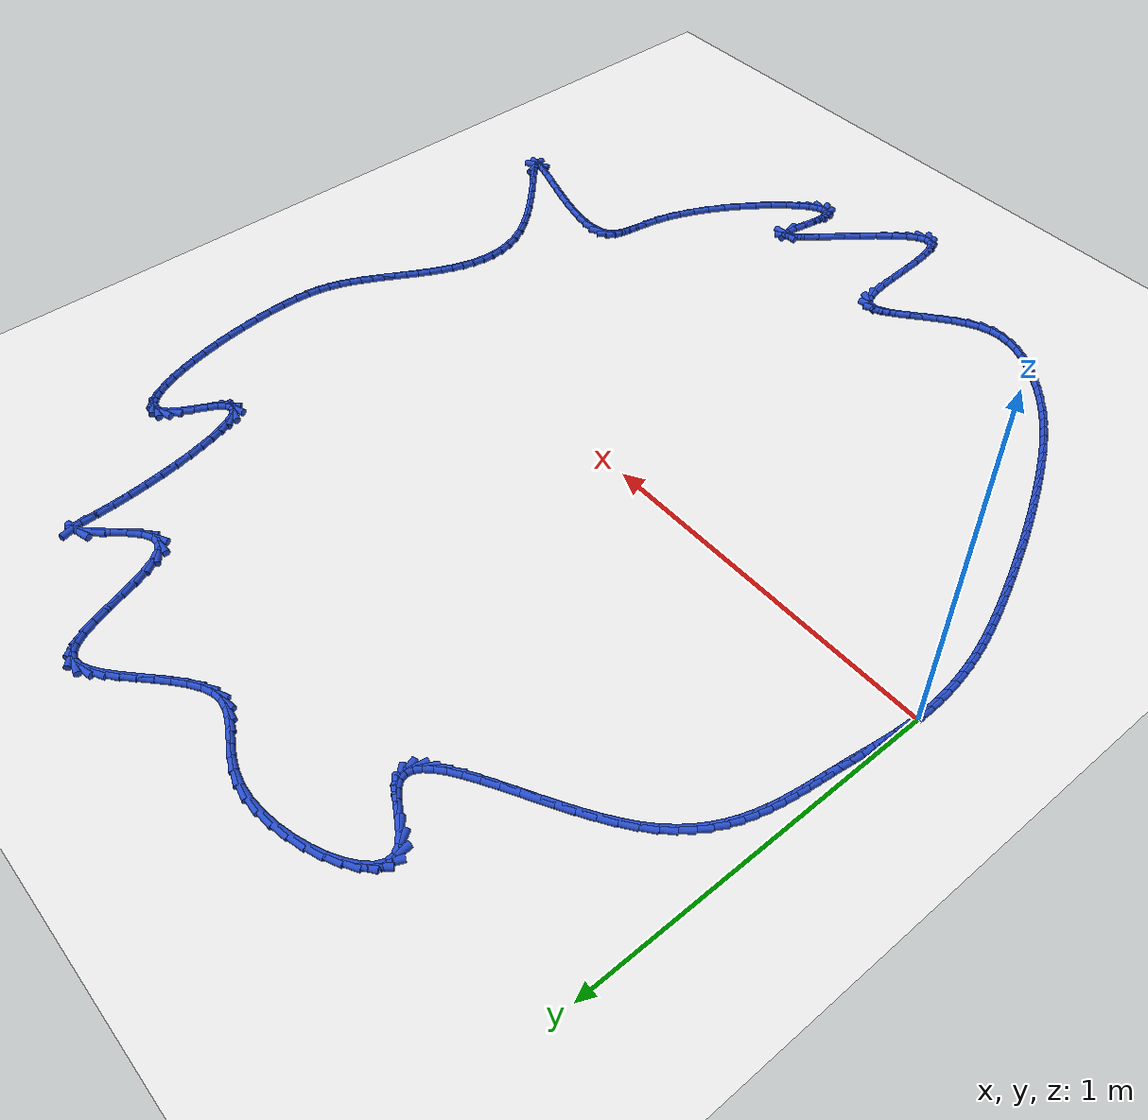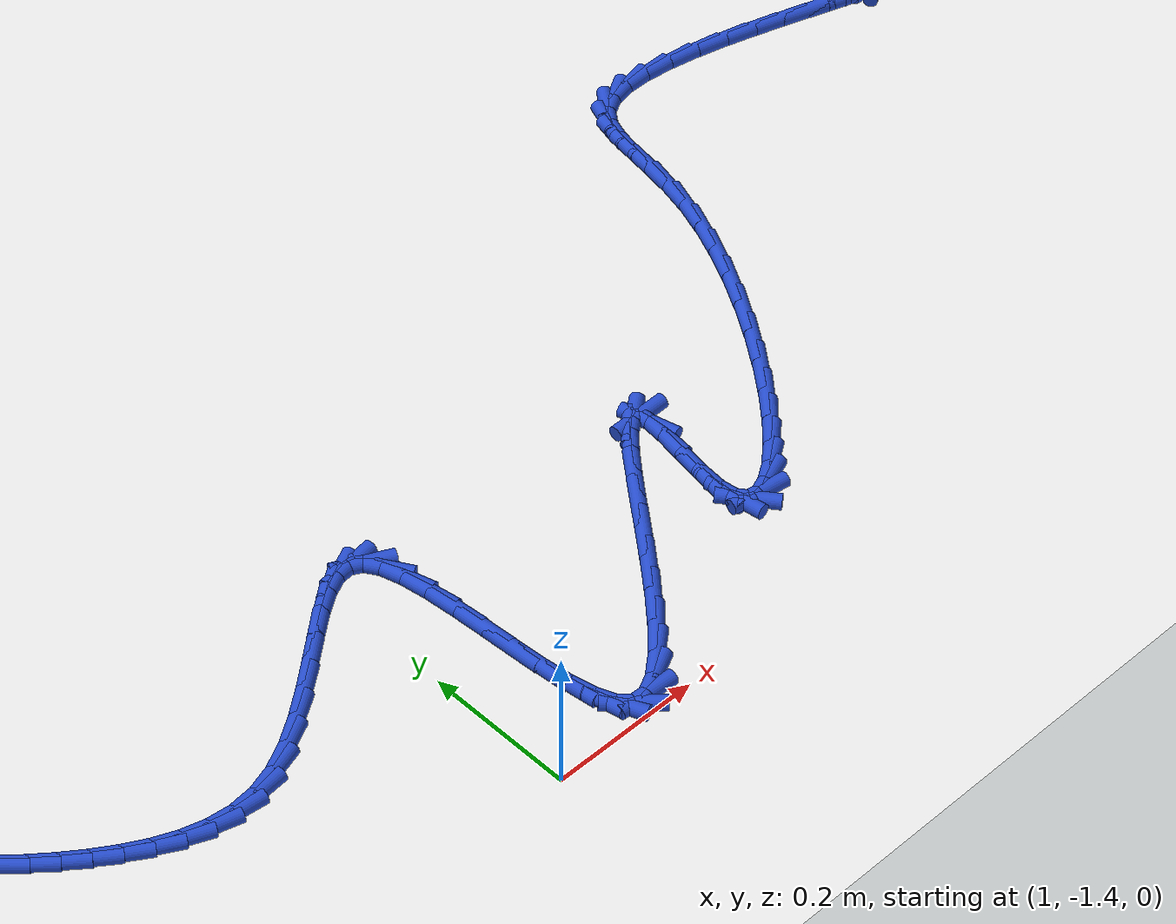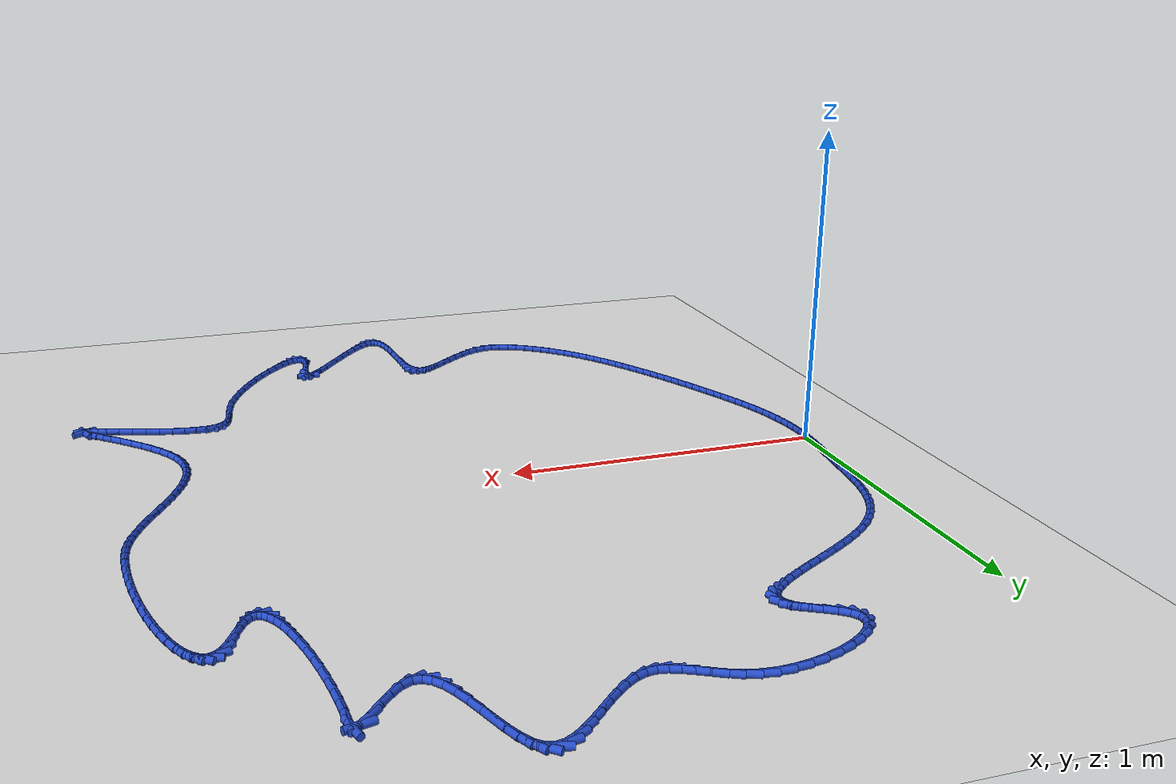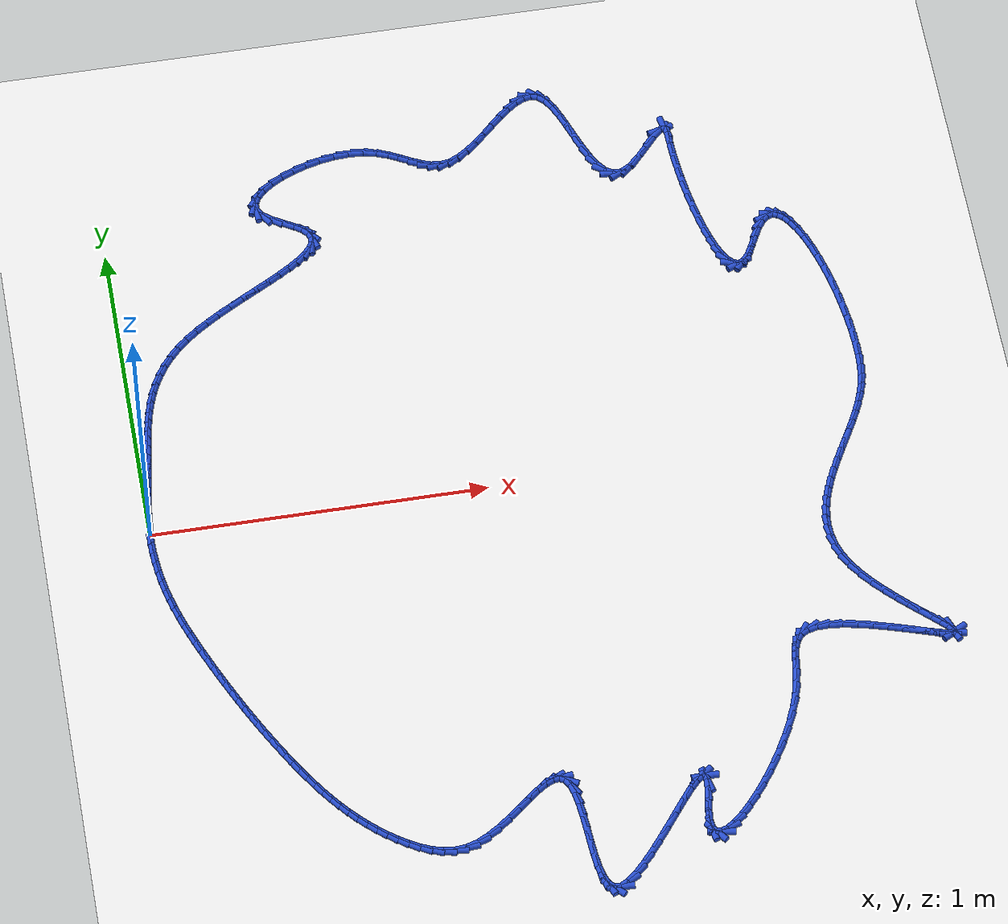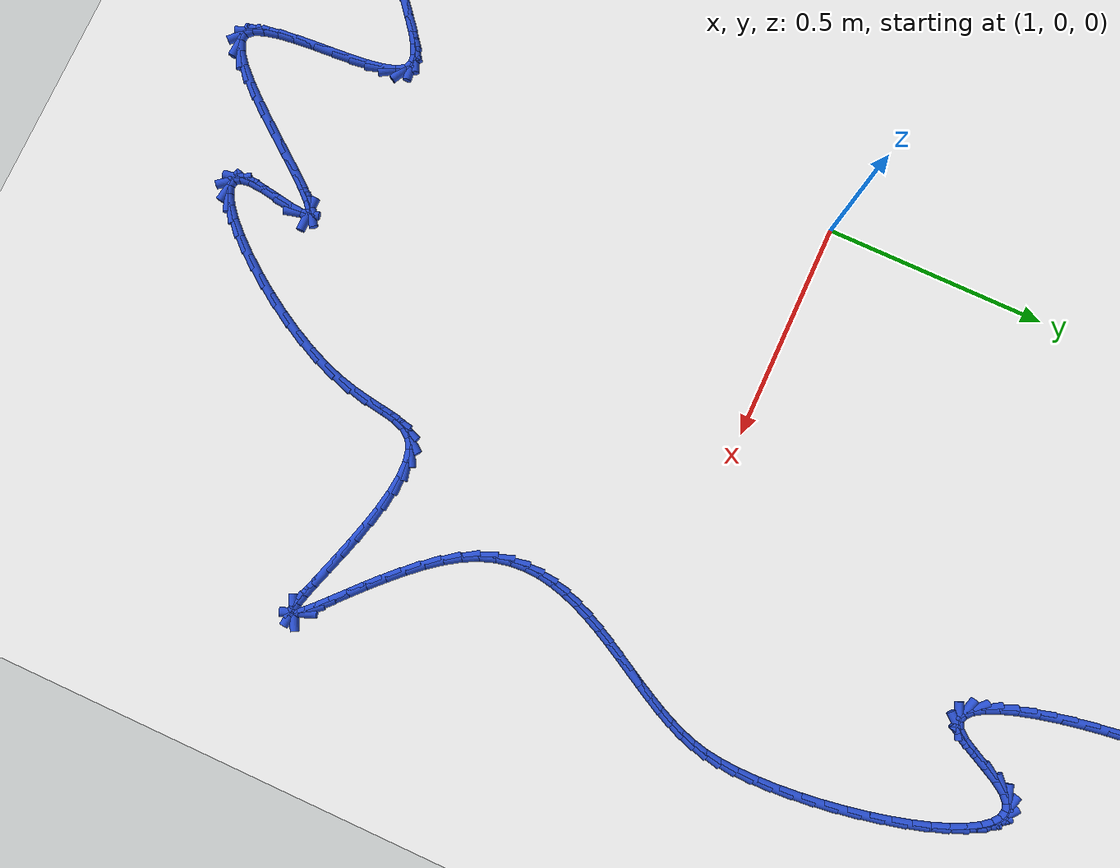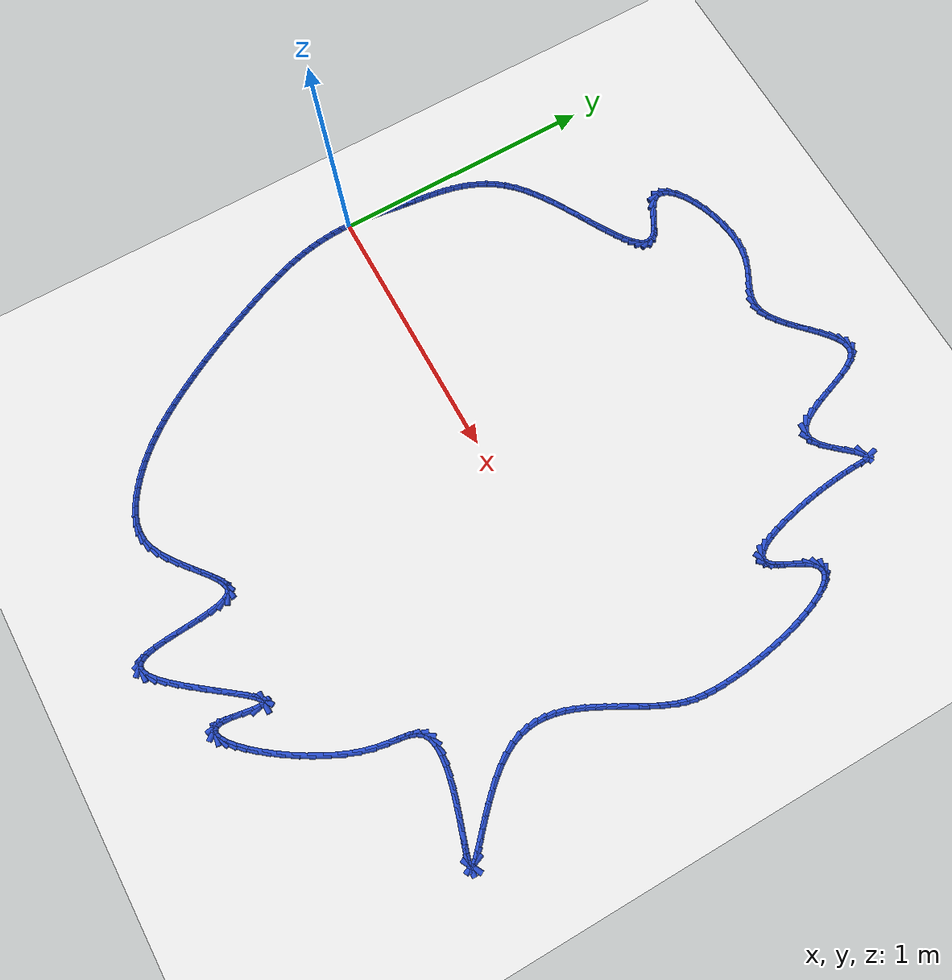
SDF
<sdf version="1.6">
 <world name="default">
  <light name="sun" type="directional">
   <pose>0 0 10 0 -0 0</pose>
   <diffuse>0.8 0.8 0.8 1</diffuse>
   <specular>0.2 0.2 0.2 1</specular>
   <attenuation>
    <range>1000</range>
    <constant>0.9</constant>
    <linear>0.01</linear>
    <quadratic>0.001</quadratic>
   </attenuation>
   <direction>-0.5 0.1 -0.9</direction>
  </light>
  <model name="ground_plane">
   <static>1</static>
   <link name="link">
    <collision name="collision">
     <geometry><plane><normal>0 0 1</normal><size>100 100</size></plane></geometry>
     <surface><friction><ode><mu>100</mu><mu2>50</mu2></ode></friction></surface>
    </collision>
    <visual name="visual">
     <cast_shadows>0</cast_shadows>
     <geometry><plane><normal>0 0 1</normal><size>100 100</size></plane></geometry>
     <material>
      <script><uri>file://media/materials/scripts/gazebo.material</uri><name>Gazebo/WhiteGlow</name></script>
     </material>
    </visual>
   </link>
  </model>
  <gravity>0 0 -9.8</gravity>
  <magnetic_field>6e-06 2.3e-05 -4.2e-05</magnetic_field>
  <atmosphere type="adiabatic"/>
  <physics name="default_physics" default="0" type="ode">
   <max_step_size>0.001</max_step_size>
   <real_time_factor>1</real_time_factor>
   <real_time_update_rate>1000</real_time_update_rate>
  </physics>
  <scene><ambient>0.4 0.4 0.4 1</ambient><background>0.7 0.7 0.7 1</background><shadows>1</shadows></scene>
  <spherical_coordinates>
   <surface_model>EARTH_WGS84</surface_model>
   <latitude_deg>0</latitude_deg>
   <longitude_deg>0</longitude_deg>
   <elevation>0</elevation>
   <heading_deg>0</heading_deg>
  </spherical_coordinates>
  <model name="line">
   <link name="link_0">
    <pose>-1.474514954580286e-17 -7.632783294297951e-17 0.01 0 1.57 1.522252228233526</pose>
    <collision name="collision">
     <geometry><cylinder><radius>0.01</radius><length>0.08</length></cylinder></geometry>
    </collision>
    <visual name="visual">
     <material>
      <script><name>Gazebo/Blue</name><uri>file://media/materials/scripts/gazebo.material</uri></script>
     </material>
     <geometry><cylinder><radius>0.01</radius><length>0.08</length></cylinder></geometry>
    </visual>
   </link>
   <link name="link_1">
    <pose>0.001594486590139592 0.03282034182620537 0.01 0 1.57 1.486663738809793</pose>
    <collision name="collision">
     <geometry><cylinder><radius>0.01</radius><length>0.08</length></cylinder></geometry>
    </collision>
    <visual name="visual">
     <material>
      <script><name>Gazebo/Blue</name><uri>file://media/materials/scripts/gazebo.material</uri></script>
     </material>
     <geometry><cylinder><radius>0.01</radius><length>0.08</length></cylinder></geometry>
    </visual>
   </link>
   <link name="link_2">
    <pose>0.0043560150522412204 0.0655663896549546 0.01 0 1.57 1.4596301122428685</pose>
    <collision name="collision">
     <geometry><cylinder><radius>0.01</radius><length>0.08</length></cylinder></geometry>
    </collision>
    <visual name="visual">
     <material>
      <script><name>Gazebo/Blue</name><uri>file://media/materials/scripts/gazebo.material</uri></script>
     </material>
     <geometry><cylinder><radius>0.01</radius><length>0.08</length></cylinder></geometry>
    </visual>
   </link>
   <link name="link_3">
    <pose>0.008004385153682859 0.09825014124045076 0.01 0 1.57 1.4411397650320492</pose>
    <collision name="collision">
     <geometry><cylinder><radius>0.01</radius><length>0.08</length></cylinder></geometry>
    </collision>
    <visual name="visual">
     <material>
      <script><name>Gazebo/Blue</name><uri>file://media/materials/scripts/gazebo.material</uri></script>
     </material>
     <geometry><cylinder><radius>0.01</radius><length>0.08</length></cylinder></geometry>
    </visual>
   </link>
   <link name="link_4">
    <pose>0.012259396661842493 0.13088359433689703 0.01 0 1.57 1.43115486098183</pose>
    <collision name="collision">
     <geometry><cylinder><radius>0.01</radius><length>0.08</length></cylinder></geometry>
    </collision>
    <visual name="visual">
     <material>
      <script><name>Gazebo/Blue</name><uri>file://media/materials/scripts/gazebo.material</uri></script>
     </material>
     <geometry><cylinder><radius>0.01</radius><length>0.08</length></cylinder></geometry>
    </visual>
   </link>
   <link name="link_5">
    <pose>0.016840849344098123 0.16347874669849666 0.01 0 1.57 1.4296515797149136</pose>
    <collision name="collision">
     <geometry><cylinder><radius>0.01</radius><length>0.08</length></cylinder></geometry>
    </collision>
    <visual name="visual">
     <material>
      <script><name>Gazebo/Blue</name><uri>file://media/materials/scripts/gazebo.material</uri></script>
     </material>
     <geometry><cylinder><radius>0.01</radius><length>0.08</length></cylinder></geometry>
    </visual>
   </link>
   <link name="link_6">
    <pose>0.021468542967827735 0.1960475960794527 0.01 0 1.57 1.436621249894222</pose>
    <collision name="collision">
     <geometry><cylinder><radius>0.01</radius><length>0.08</length></cylinder></geometry>
    </collision>
    <visual name="visual">
     <material>
      <script><name>Gazebo/Blue</name><uri>file://media/materials/scripts/gazebo.material</uri></script>
     </material>
     <geometry><cylinder><radius>0.01</radius><length>0.08</length></cylinder></geometry>
    </visual>
   </link>
   <link name="link_7">
    <pose>0.025862943481214845 0.2286020628535499 0.01 0 1.57 1.4469512849292223</pose>
    <collision name="collision">
     <geometry><cylinder><radius>0.01</radius><length>0.08</length></cylinder></geometry>
    </collision>
    <visual name="visual">
     <material>
      <script><name>Gazebo/Blue</name><uri>file://media/materials/scripts/gazebo.material</uri></script>
     </material>
     <geometry><cylinder><radius>0.01</radius><length>0.08</length></cylinder></geometry>
    </visual>
   </link>
   <link name="link_8">
    <pose>0.029912654618215108 0.26113453730283015 0.01 0 1.57 1.4486952721358533</pose>
    <collision name="collision">
     <geometry><cylinder><radius>0.01</radius><length>0.08</length></cylinder></geometry>
    </collision>
    <visual name="visual">
     <material>
      <script><name>Gazebo/Blue</name><uri>file://media/materials/scripts/gazebo.material</uri></script>
     </material>
     <geometry><cylinder><radius>0.01</radius><length>0.08</length></cylinder></geometry>
    </visual>
   </link>
   <link name="link_9">
    <pose>0.0338955813603054 0.2935921903135608 0.01 0 1.57 1.4400941703268968</pose>
    <collision name="collision">
     <geometry><cylinder><radius>0.01</radius><length>0.08</length></cylinder></geometry>
    </collision>
    <visual name="visual">
     <material>
      <script><name>Gazebo/Blue</name><uri>file://media/materials/scripts/gazebo.material</uri></script>
     </material>
     <geometry><cylinder><radius>0.01</radius><length>0.08</length></cylinder></geometry>
    </visual>
   </link>
   <link name="link_10">
    <pose>0.03814457111847164 0.32591581091867433 0.01 0 1.57 1.4210437590948073</pose>
    <collision name="collision">
     <geometry><cylinder><radius>0.01</radius><length>0.08</length></cylinder></geometry>
    </collision>
    <visual name="visual">
     <material>
      <script><name>Gazebo/Blue</name><uri>file://media/materials/scripts/gazebo.material</uri></script>
     </material>
     <geometry><cylinder><radius>0.01</radius><length>0.08</length></cylinder></geometry>
    </visual>
   </link>
   <link name="link_11">
    <pose>0.042992471303699764 0.358046188151103 0.01 0 1.57 1.3914386838464063</pose>
    <collision name="collision">
     <geometry><cylinder><radius>0.01</radius><length>0.08</length></cylinder></geometry>
    </collision>
    <visual name="visual">
     <material>
      <script><name>Gazebo/Blue</name><uri>file://media/materials/scripts/gazebo.material</uri></script>
     </material>
     <geometry><cylinder><radius>0.01</radius><length>0.08</length></cylinder></geometry>
    </visual>
   </link>
   <link name="link_12">
    <pose>0.0487721293269757 0.38992411104377905 0.01 0 1.57 1.351235805734445</pose>
    <collision name="collision">
     <geometry><cylinder><radius>0.01</radius><length>0.08</length></cylinder></geometry>
    </collision>
    <visual name="visual">
     <material>
      <script><name>Gazebo/Blue</name><uri>file://media/materials/scripts/gazebo.material</uri></script>
     </material>
     <geometry><cylinder><radius>0.01</radius><length>0.08</length></cylinder></geometry>
    </visual>
   </link>
   <link name="link_13">
    <pose>0.055816392599285385 0.4214903686296349 0.01 0 1.57 1.3005539609662147</pose>
    <collision name="collision">
     <geometry><cylinder><radius>0.01</radius><length>0.08</length></cylinder></geometry>
    </collision>
    <visual name="visual">
     <material>
      <script><name>Gazebo/Blue</name><uri>file://media/materials/scripts/gazebo.material</uri></script>
     </material>
     <geometry><cylinder><radius>0.01</radius><length>0.08</length></cylinder></geometry>
    </visual>
   </link>
   <link name="link_14">
    <pose>0.06445810853161471 0.4526857499416027 0.01 0 1.57 1.2398035609341025</pose>
    <collision name="collision">
     <geometry><cylinder><radius>0.01</radius><length>0.08</length></cylinder></geometry>
    </collision>
    <visual name="visual">
     <material>
      <script><name>Gazebo/Blue</name><uri>file://media/materials/scripts/gazebo.material</uri></script>
     </material>
     <geometry><cylinder><radius>0.01</radius><length>0.08</length></cylinder></geometry>
    </visual>
   </link>
   <link name="link_15">
    <pose>0.07503012453494966 0.483451044012615 0.01 0 1.57 1.1698250328970665</pose>
    <collision name="collision">
     <geometry><cylinder><radius>0.01</radius><length>0.08</length></cylinder></geometry>
    </collision>
    <visual name="visual">
     <material>
      <script><name>Gazebo/Blue</name><uri>file://media/materials/scripts/gazebo.material</uri></script>
     </material>
     <geometry><cylinder><radius>0.01</radius><length>0.08</length></cylinder></geometry>
    </visual>
   </link>
   <link name="link_16">
    <pose>0.08786528802027616 0.5137270398756042 0.01 0 1.57 1.0919958025029497</pose>
    <collision name="collision">
     <geometry><cylinder><radius>0.01</radius><length>0.08</length></cylinder></geometry>
    </collision>
    <visual name="visual">
     <material>
      <script><name>Gazebo/Blue</name><uri>file://media/materials/scripts/gazebo.material</uri></script>
     </material>
     <geometry><cylinder><radius>0.01</radius><length>0.08</length></cylinder></geometry>
    </visual>
   </link>
   <link name="link_17">
    <pose>0.10329644639858007 0.5434545265635022 0.01 0 1.57 1.0082520261159904</pose>
    <collision name="collision">
     <geometry><cylinder><radius>0.01</radius><length>0.08</length></cylinder></geometry>
    </collision>
    <visual name="visual">
     <material>
      <script><name>Gazebo/Blue</name><uri>file://media/materials/scripts/gazebo.material</uri></script>
     </material>
     <geometry><cylinder><radius>0.01</radius><length>0.08</length></cylinder></geometry>
    </visual>
   </link>
   <link name="link_18">
    <pose>0.12165644708084737 0.5725742931092419 0.01 0 1.57 0.9209807847451601</pose>
    <collision name="collision">
     <geometry><cylinder><radius>0.01</radius><length>0.08</length></cylinder></geometry>
    </collision>
    <visual name="visual">
     <material>
      <script><name>Gazebo/Blue</name><uri>file://media/materials/scripts/gazebo.material</uri></script>
     </material>
     <geometry><cylinder><radius>0.01</radius><length>0.08</length></cylinder></geometry>
    </visual>
   </link>
   <link name="link_19">
    <pose>0.14327813747806398 0.6010271285457549 0.01 0 1.57 0.8327810190407866</pose>
    <collision name="collision">
     <geometry><cylinder><radius>0.01</radius><length>0.08</length></cylinder></geometry>
    </collision>
    <visual name="visual">
     <material>
      <script><name>Gazebo/Blue</name><uri>file://media/materials/scripts/gazebo.material</uri></script>
     </material>
     <geometry><cylinder><radius>0.01</radius><length>0.08</length></cylinder></geometry>
    </visual>
   </link>
   <link name="link_20">
    <pose>0.16849436500121587 0.6287538219059743 0.01 0 1.57 0.746151612944165</pose>
    <collision name="collision">
     <geometry><cylinder><radius>0.01</radius><length>0.08</length></cylinder></geometry>
    </collision>
    <visual name="visual">
     <material>
      <script><name>Gazebo/Blue</name><uri>file://media/materials/scripts/gazebo.material</uri></script>
     </material>
     <geometry><cylinder><radius>0.01</radius><length>0.08</length></cylinder></geometry>
    </visual>
   </link>
   <link name="link_21">
    <pose>0.19763797706098726 0.6556951622228544 0.01 0 1.57 0.6666109694723344</pose>
    <collision name="collision">
     <geometry><cylinder><radius>0.01</radius><length>0.08</length></cylinder></geometry>
    </collision>
    <visual name="visual">
     <material>
      <script><name>Gazebo/Blue</name><uri>file://media/materials/scripts/gazebo.material</uri></script>
     </material>
     <geometry><cylinder><radius>0.01</radius><length>0.08</length></cylinder></geometry>
    </visual>
   </link>
   <link name="link_22">
    <pose>0.23082832609378992 0.6818077593660807 0.01 0 1.57 0.6061113140481886</pose>
    <collision name="collision">
     <geometry><cylinder><radius>0.01</radius><length>0.08</length></cylinder></geometry>
    </collision>
    <visual name="visual">
     <material>
      <script><name>Gazebo/Blue</name><uri>file://media/materials/scripts/gazebo.material</uri></script>
     </material>
     <geometry><cylinder><radius>0.01</radius><length>0.08</length></cylinder></geometry>
    </visual>
   </link>
   <link name="link_23">
    <pose>0.2673336578916968 0.7071112936326716 0.01 0 1.57 0.5628801227923164</pose>
    <collision name="collision">
     <geometry><cylinder><radius>0.01</radius><length>0.08</length></cylinder></geometry>
    </collision>
    <visual name="visual">
     <material>
      <script><name>Gazebo/Blue</name><uri>file://media/materials/scripts/gazebo.material</uri></script>
     </material>
     <geometry><cylinder><radius>0.01</radius><length>0.08</length></cylinder></geometry>
    </visual>
   </link>
   <link name="link_24">
    <pose>0.30621015748373703 0.7316411598755518 0.01 0 1.57 0.5332608298058857</pose>
    <collision name="collision">
     <geometry><cylinder><radius>0.01</radius><length>0.08</length></cylinder></geometry>
    </collision>
    <visual name="visual">
     <material>
      <script><name>Gazebo/Blue</name><uri>file://media/materials/scripts/gazebo.material</uri></script>
     </material>
     <geometry><cylinder><radius>0.01</radius><length>0.08</length></cylinder></geometry>
    </visual>
   </link>
   <link name="link_25">
    <pose>0.34651400989894005 0.7554327529476479 0.01 0 1.57 0.51510090493418</pose>
    <collision name="collision">
     <geometry><cylinder><radius>0.01</radius><length>0.08</length></cylinder></geometry>
    </collision>
    <visual name="visual">
     <material>
      <script><name>Gazebo/Blue</name><uri>file://media/materials/scripts/gazebo.material</uri></script>
     </material>
     <geometry><cylinder><radius>0.01</radius><length>0.08</length></cylinder></geometry>
    </visual>
   </link>
   <link name="link_26">
    <pose>0.38730140016633474 0.7785214677018841 0.01 0 1.57 0.5074258716123596</pose>
    <collision name="collision">
     <geometry><cylinder><radius>0.01</radius><length>0.08</length></cylinder></geometry>
    </collision>
    <visual name="visual">
     <material>
      <script><name>Gazebo/Blue</name><uri>file://media/materials/scripts/gazebo.material</uri></script>
     </material>
     <geometry><cylinder><radius>0.01</radius><length>0.08</length></cylinder></geometry>
    </visual>
   </link>
   <link name="link_27">
    <pose>0.4276285133149505 0.8009426989911869 0.01 0 1.57 0.5103367497982298</pose>
    <collision name="collision">
     <geometry><cylinder><radius>0.01</radius><length>0.08</length></cylinder></geometry>
    </collision>
    <visual name="visual">
     <material>
      <script><name>Gazebo/Blue</name><uri>file://media/materials/scripts/gazebo.material</uri></script>
     </material>
     <geometry><cylinder><radius>0.01</radius><length>0.08</length></cylinder></geometry>
    </visual>
   </link>
   <link name="link_28">
    <pose>0.46655153437381647 0.8227318416684809 0.01 0 1.57 0.5251516550084752</pose>
    <collision name="collision">
     <geometry><cylinder><radius>0.01</radius><length>0.08</length></cylinder></geometry>
    </collision>
    <visual name="visual">
     <material>
      <script><name>Gazebo/Blue</name><uri>file://media/materials/scripts/gazebo.material</uri></script>
     </material>
     <geometry><cylinder><radius>0.01</radius><length>0.08</length></cylinder></geometry>
    </visual>
   </link>
   <link name="link_29">
    <pose>0.5031266483719617 0.8439242905866919 0.01 0 1.57 0.5548969094050655</pose>
    <collision name="collision">
     <geometry><cylinder><radius>0.01</radius><length>0.08</length></cylinder></geometry>
    </collision>
    <visual name="visual">
     <material>
      <script><name>Gazebo/Blue</name><uri>file://media/materials/scripts/gazebo.material</uri></script>
     </material>
     <geometry><cylinder><radius>0.01</radius><length>0.08</length></cylinder></geometry>
    </visual>
   </link>
   <link name="link_30">
    <pose>0.5364100403384159 0.8645554405987456 0.01 0 1.57 0.6054327755974536</pose>
    <collision name="collision">
     <geometry><cylinder><radius>0.01</radius><length>0.08</length></cylinder></geometry>
    </collision>
    <visual name="visual">
     <material>
      <script><name>Gazebo/Blue</name><uri>file://media/materials/scripts/gazebo.material</uri></script>
     </material>
     <geometry><cylinder><radius>0.01</radius><length>0.08</length></cylinder></geometry>
    </visual>
   </link>
   <link name="link_31">
    <pose>0.5654578953022078 0.884660686557567 0.01 0 1.57 0.687883019826923</pose>
    <collision name="collision">
     <geometry><cylinder><radius>0.01</radius><length>0.08</length></cylinder></geometry>
    </collision>
    <visual name="visual">
     <material>
      <script><name>Gazebo/Blue</name><uri>file://media/materials/scripts/gazebo.material</uri></script>
     </material>
     <geometry><cylinder><radius>0.01</radius><length>0.08</length></cylinder></geometry>
    </visual>
   </link>
   <link name="link_32">
    <pose>0.5893263982923668 0.9042754233160819 0.01 0 1.57 0.823701813937166</pose>
    <collision name="collision">
     <geometry><cylinder><radius>0.01</radius><length>0.08</length></cylinder></geometry>
    </collision>
    <visual name="visual">
     <material>
      <script><name>Gazebo/Blue</name><uri>file://media/materials/scripts/gazebo.material</uri></script>
     </material>
     <geometry><cylinder><radius>0.01</radius><length>0.08</length></cylinder></geometry>
    </visual>
   </link>
   <link name="link_33">
    <pose>0.607071734337922 0.9234350457272154 0.01 0 1.57 1.05286436707155</pose>
    <collision name="collision">
     <geometry><cylinder><radius>0.01</radius><length>0.08</length></cylinder></geometry>
    </collision>
    <visual name="visual">
     <material>
      <script><name>Gazebo/Blue</name><uri>file://media/materials/scripts/gazebo.material</uri></script>
     </material>
     <geometry><cylinder><radius>0.01</radius><length>0.08</length></cylinder></geometry>
    </visual>
   </link>
   <link name="link_34">
    <pose>0.6177500884679024 0.9421749486438928 0.01 0 1.57 1.4264798606076436</pose>
    <collision name="collision">
     <geometry><cylinder><radius>0.01</radius><length>0.08</length></cylinder></geometry>
    </collision>
    <visual name="visual">
     <material>
      <script><name>Gazebo/Blue</name><uri>file://media/materials/scripts/gazebo.material</uri></script>
     </material>
     <geometry><cylinder><radius>0.01</radius><length>0.08</length></cylinder></geometry>
    </visual>
   </link>
   <link name="link_35">
    <pose>0.6204176457113377 0.9605305269190401 0.01 0 1.57 -1.234877298194461</pose>
    <collision name="collision">
     <geometry><cylinder><radius>0.01</radius><length>0.08</length></cylinder></geometry>
    </collision>
    <visual name="visual">
     <material>
      <script><name>Gazebo/Blue</name><uri>file://media/materials/scripts/gazebo.material</uri></script>
     </material>
     <geometry><cylinder><radius>0.01</radius><length>0.08</length></cylinder></geometry>
    </visual>
   </link>
   <link name="link_36">
    <pose>0.6141305910972567 0.9785371754055822 0.01 0 1.57 -0.8298698635083949</pose>
    <collision name="collision">
     <geometry><cylinder><radius>0.01</radius><length>0.08</length></cylinder></geometry>
    </collision>
    <visual name="visual">
     <material>
      <script><name>Gazebo/Blue</name><uri>file://media/materials/scripts/gazebo.material</uri></script>
     </material>
     <geometry><cylinder><radius>0.01</radius><length>0.08</length></cylinder></geometry>
    </visual>
   </link>
   <link name="link_37">
    <pose>0.5979451102330804 0.9962302889912633 0.01 0 1.57 -0.5935095443921917</pose>
    <collision name="collision">
     <geometry><cylinder><radius>0.01</radius><length>0.08</length></cylinder></geometry>
    </collision>
    <visual name="visual">
     <material>
      <script><name>Gazebo/Blue</name><uri>file://media/materials/scripts/gazebo.material</uri></script>
     </material>
     <geometry><cylinder><radius>0.01</radius><length>0.08</length></cylinder></geometry>
    </visual>
   </link>
   <link name="link_38">
    <pose>0.5720323019005138 1.0137123788299907 0.01 0 1.57 -0.5156206917234994</pose>
    <collision name="collision">
     <geometry><cylinder><radius>0.01</radius><length>0.08</length></cylinder></geometry>
    </collision>
    <visual name="visual">
     <material>
      <script><name>Gazebo/Blue</name><uri>file://media/materials/scripts/gazebo.material</uri></script>
     </material>
     <geometry><cylinder><radius>0.01</radius><length>0.08</length></cylinder></geometry>
    </visual>
   </link>
   <link name="link_39">
    <pose>0.5409158596136892 1.0313479763955526 0.01 0 1.57 -0.5350662135061496</pose>
    <collision name="collision">
     <geometry><cylinder><radius>0.01</radius><length>0.08</length></cylinder></geometry>
    </collision>
    <visual name="visual">
     <material>
      <script><name>Gazebo/Blue</name><uri>file://media/materials/scripts/gazebo.material</uri></script>
     </material>
     <geometry><cylinder><radius>0.01</radius><length>0.08</length></cylinder></geometry>
    </visual>
   </link>
   <link name="link_40">
    <pose>0.5101815005371514 1.0495655455500494 0.01 0 1.57 -0.6601652004081842</pose>
    <collision name="collision">
     <geometry><cylinder><radius>0.01</radius><length>0.08</length></cylinder></geometry>
    </collision>
    <visual name="visual">
     <material>
      <script><name>Gazebo/Blue</name><uri>file://media/materials/scripts/gazebo.material</uri></script>
     </material>
     <geometry><cylinder><radius>0.01</radius><length>0.08</length></cylinder></geometry>
    </visual>
   </link>
   <link name="link_41">
    <pose>0.48541494183544376 1.0687935501555816 0.01 0 1.57 -0.9895298242675746</pose>
    <collision name="collision">
     <geometry><cylinder><radius>0.01</radius><length>0.08</length></cylinder></geometry>
    </collision>
    <visual name="visual">
     <material>
      <script><name>Gazebo/Blue</name><uri>file://media/materials/scripts/gazebo.material</uri></script>
     </material>
     <geometry><cylinder><radius>0.01</radius><length>0.08</length></cylinder></geometry>
    </visual>
   </link>
   <link name="link_42">
    <pose>0.47187066933684363 1.0894095057613276 0.01 0 1.57 -1.521019702727373</pose>
    <collision name="collision">
     <geometry><cylinder><radius>0.01</radius><length>0.08</length></cylinder></geometry>
    </collision>
    <visual name="visual">
     <material>
      <script><name>Gazebo/Blue</name><uri>file://media/materials/scripts/gazebo.material</uri></script>
     </material>
     <geometry><cylinder><radius>0.01</radius><length>0.08</length></cylinder></geometry>
    </visual>
   </link>
   <link name="link_43">
    <pose>0.47078645560347976 1.111173097590661 0.01 0 1.57 1.1507806061834411</pose>
    <collision name="collision">
     <geometry><cylinder><radius>0.01</radius><length>0.08</length></cylinder></geometry>
    </collision>
    <visual name="visual">
     <material>
      <script><name>Gazebo/Blue</name><uri>file://media/materials/scripts/gazebo.material</uri></script>
     </material>
     <geometry><cylinder><radius>0.01</radius><length>0.08</length></cylinder></geometry>
    </visual>
   </link>
   <link name="link_44">
    <pose>0.48072750543279236 1.1334329301391615 0.01 0 1.57 0.8481830789989516</pose>
    <collision name="collision">
     <geometry><cylinder><radius>0.01</radius><length>0.08</length></cylinder></geometry>
    </collision>
    <visual name="visual">
     <material>
      <script><name>Gazebo/Blue</name><uri>file://media/materials/scripts/gazebo.material</uri></script>
     </material>
     <geometry><cylinder><radius>0.01</radius><length>0.08</length></cylinder></geometry>
    </visual>
   </link>
   <link name="link_45">
    <pose>0.5002106893241229 1.1555301733674623 0.01 0 1.57 0.657734537447775</pose>
    <collision name="collision">
     <geometry><cylinder><radius>0.01</radius><length>0.08</length></cylinder></geometry>
    </collision>
    <visual name="visual">
     <material>
      <script><name>Gazebo/Blue</name><uri>file://media/materials/scripts/gazebo.material</uri></script>
     </material>
     <geometry><cylinder><radius>0.01</radius><length>0.08</length></cylinder></geometry>
    </visual>
   </link>
   <link name="link_46">
    <pose>0.5277528777768132 1.1768059972361982 0.01 0 1.57 0.5257394450936792</pose>
    <collision name="collision">
     <geometry><cylinder><radius>0.01</radius><length>0.08</length></cylinder></geometry>
    </collision>
    <visual name="visual">
     <material>
      <script><name>Gazebo/Blue</name><uri>file://media/materials/scripts/gazebo.material</uri></script>
     </material>
     <geometry><cylinder><radius>0.01</radius><length>0.08</length></cylinder></geometry>
    </visual>
   </link>
   <link name="link_47">
    <pose>0.5618709412902047 1.1966015717060023 0.01 0 1.57 0.42310057324134015</pose>
    <collision name="collision">
     <geometry><cylinder><radius>0.01</radius><length>0.08</length></cylinder></geometry>
    </collision>
    <visual name="visual">
     <material>
      <script><name>Gazebo/Blue</name><uri>file://media/materials/scripts/gazebo.material</uri></script>
     </material>
     <geometry><cylinder><radius>0.01</radius><length>0.08</length></cylinder></geometry>
    </visual>
   </link>
   <link name="link_48">
    <pose>0.6010817503636389 1.2142580667375094 0.01 0 1.57 0.33399759228434717</pose>
    <collision name="collision">
     <geometry><cylinder><radius>0.01</radius><length>0.08</length></cylinder></geometry>
    </collision>
    <visual name="visual">
     <material>
      <script><name>Gazebo/Blue</name><uri>file://media/materials/scripts/gazebo.material</uri></script>
     </material>
     <geometry><cylinder><radius>0.01</radius><length>0.08</length></cylinder></geometry>
    </visual>
   </link>
   <link name="link_49">
    <pose>0.6439021754964571 1.229116652291352 0.01 0 1.57 0.2484331930736362</pose>
    <collision name="collision">
     <geometry><cylinder><radius>0.01</radius><length>0.08</length></cylinder></geometry>
    </collision>
    <visual name="visual">
     <material>
      <script><name>Gazebo/Blue</name><uri>file://media/materials/scripts/gazebo.material</uri></script>
     </material>
     <geometry><cylinder><radius>0.01</radius><length>0.08</length></cylinder></geometry>
    </visual>
   </link>
   <link name="link_50">
    <pose>0.6888490871880016 1.2405184983281652 0.01 0 1.57 0.1584805999678742</pose>
    <collision name="collision">
     <geometry><cylinder><radius>0.01</radius><length>0.08</length></cylinder></geometry>
    </collision>
    <visual name="visual">
     <material>
      <script><name>Gazebo/Blue</name><uri>file://media/materials/scripts/gazebo.material</uri></script>
     </material>
     <geometry><cylinder><radius>0.01</radius><length>0.08</length></cylinder></geometry>
    </visual>
   </link>
   <link name="link_51">
    <pose>0.7344393559376131 1.2478047748085825 0.01 0 1.57 0.05607186617904562</pose>
    <collision name="collision">
     <geometry><cylinder><radius>0.01</radius><length>0.08</length></cylinder></geometry>
    </collision>
    <visual name="visual">
     <material>
      <script><name>Gazebo/Blue</name><uri>file://media/materials/scripts/gazebo.material</uri></script>
     </material>
     <geometry><cylinder><radius>0.01</radius><length>0.08</length></cylinder></geometry>
    </visual>
   </link>
   <link name="link_52">
    <pose>0.779189852244634 1.2503166516932378 0.01 0 1.57 -0.06874651175645971</pose>
    <collision name="collision">
     <geometry><cylinder><radius>0.01</radius><length>0.08</length></cylinder></geometry>
    </collision>
    <visual name="visual">
     <material>
      <script><name>Gazebo/Blue</name><uri>file://media/materials/scripts/gazebo.material</uri></script>
     </material>
     <geometry><cylinder><radius>0.01</radius><length>0.08</length></cylinder></geometry>
    </visual>
   </link>
   <link name="link_53">
    <pose>0.8216174466084052 1.2473952989427648 0.01 0 1.57 -0.2224485323440739</pose>
    <collision name="collision">
     <geometry><cylinder><radius>0.01</radius><length>0.08</length></cylinder></geometry>
    </collision>
    <visual name="visual">
     <material>
      <script><name>Gazebo/Blue</name><uri>file://media/materials/scripts/gazebo.material</uri></script>
     </material>
     <geometry><cylinder><radius>0.01</radius><length>0.08</length></cylinder></geometry>
    </visual>
   </link>
   <link name="link_54">
    <pose>0.860423576662155 1.2386176702272482 0.01 0 1.57 -0.3609227639666346</pose>
    <collision name="collision">
     <geometry><cylinder><radius>0.01</radius><length>0.08</length></cylinder></geometry>
    </collision>
    <visual name="visual">
     <material>
      <script><name>Gazebo/Blue</name><uri>file://media/materials/scripts/gazebo.material</uri></script>
     </material>
     <geometry><cylinder><radius>0.01</radius><length>0.08</length></cylinder></geometry>
    </visual>
   </link>
   <link name="link_55">
    <pose>0.8956791536780627 1.2253102158242453 0.01 0 1.57 -0.45192403354081095</pose>
    <collision name="collision">
     <geometry><cylinder><radius>0.01</radius><length>0.08</length></cylinder></geometry>
    </collision>
    <visual name="visual">
     <material>
      <script><name>Gazebo/Blue</name><uri>file://media/materials/scripts/gazebo.material</uri></script>
     </material>
     <geometry><cylinder><radius>0.01</radius><length>0.08</length></cylinder></geometry>
    </visual>
   </link>
   <link name="link_56">
    <pose>0.9280710133108323 1.2095862267266388 0.01 0 1.57 -0.4875642209382682</pose>
    <collision name="collision">
     <geometry><cylinder><radius>0.01</radius><length>0.08</length></cylinder></geometry>
    </collision>
    <visual name="visual">
     <material>
      <script><name>Gazebo/Blue</name><uri>file://media/materials/scripts/gazebo.material</uri></script>
     </material>
     <geometry><cylinder><radius>0.01</radius><length>0.08</length></cylinder></geometry>
    </visual>
   </link>
   <link name="link_57">
    <pose>0.9582889422901291 1.1935627639127158 0.01 0 1.57 -0.45915456723908177</pose>
    <collision name="collision">
     <geometry><cylinder><radius>0.01</radius><length>0.08</length></cylinder></geometry>
    </collision>
    <visual name="visual">
     <material>
      <script><name>Gazebo/Blue</name><uri>file://media/materials/scripts/gazebo.material</uri></script>
     </material>
     <geometry><cylinder><radius>0.01</radius><length>0.08</length></cylinder></geometry>
    </visual>
   </link>
   <link name="link_58">
    <pose>0.9870227273456179 1.179356888360764 0.01 0 1.57 -0.3522891391559436</pose>
    <collision name="collision">
     <geometry><cylinder><radius>0.01</radius><length>0.08</length></cylinder></geometry>
    </collision>
    <visual name="visual">
     <material>
      <script><name>Gazebo/Blue</name><uri>file://media/materials/scripts/gazebo.material</uri></script>
     </material>
     <geometry><cylinder><radius>0.01</radius><length>0.08</length></cylinder></geometry>
    </visual>
   </link>
   <link name="link_59">
    <pose>1.0149621552069636 1.1690856610490705 0.01 0 1.57 -0.1504457218894979</pose>
    <collision name="collision">
     <geometry><cylinder><radius>0.01</radius><length>0.08</length></cylinder></geometry>
    </collision>
    <visual name="visual">
     <material>
      <script><name>Gazebo/Blue</name><uri>file://media/materials/scripts/gazebo.material</uri></script>
     </material>
     <geometry><cylinder><radius>0.01</radius><length>0.08</length></cylinder></geometry>
    </visual>
   </link>
   <link name="link_60">
    <pose>1.0427970126038315 1.164866142955923 0.01 0 1.57 0.1370469194420273</pose>
    <collision name="collision">
     <geometry><cylinder><radius>0.01</radius><length>0.08</length></cylinder></geometry>
    </collision>
    <visual name="visual">
     <material>
      <script><name>Gazebo/Blue</name><uri>file://media/materials/scripts/gazebo.material</uri></script>
     </material>
     <geometry><cylinder><radius>0.01</radius><length>0.08</length></cylinder></geometry>
    </visual>
   </link>
   <link name="link_61">
    <pose>1.0712095542637672 1.1687845567329234 0.01 0 1.57 0.4055199991153515</pose>
    <collision name="collision">
     <geometry><cylinder><radius>0.01</radius><length>0.08</length></cylinder></geometry>
    </collision>
    <visual name="visual">
     <material>
      <script><name>Gazebo/Blue</name><uri>file://media/materials/scripts/gazebo.material</uri></script>
     </material>
     <geometry><cylinder><radius>0.01</radius><length>0.08</length></cylinder></geometry>
    </visual>
   </link>
   <link name="link_62">
    <pose>1.1004990270621036 1.1813589734190637 0.01 0 1.57 0.5770092240264024</pose>
    <collision name="collision">
     <geometry><cylinder><radius>0.01</radius><length>0.08</length></cylinder></geometry>
    </collision>
    <visual name="visual">
     <material>
      <script><name>Gazebo/Blue</name><uri>file://media/materials/scripts/gazebo.material</uri></script>
     </material>
     <geometry><cylinder><radius>0.01</radius><length>0.08</length></cylinder></geometry>
    </visual>
   </link>
   <link name="link_63">
    <pose>1.1304075750854832 1.200826514377163 0.01 0 1.57 0.6795114373392805</pose>
    <collision name="collision">
     <geometry><cylinder><radius>0.01</radius><length>0.08</length></cylinder></geometry>
    </collision>
    <visual name="visual">
     <material>
      <script><name>Gazebo/Blue</name><uri>file://media/materials/scripts/gazebo.material</uri></script>
     </material>
     <geometry><cylinder><radius>0.01</radius><length>0.08</length></cylinder></geometry>
    </visual>
   </link>
   <link name="link_64">
    <pose>1.1606334517151176 1.2252445989610576 0.01 0 1.57 0.7366154509510277</pose>
    <collision name="collision">
     <geometry><cylinder><radius>0.01</radius><length>0.08</length></cylinder></geometry>
    </collision>
    <visual name="visual">
     <material>
      <script><name>Gazebo/Blue</name><uri>file://media/materials/scripts/gazebo.material</uri></script>
     </material>
     <geometry><cylinder><radius>0.01</radius><length>0.08</length></cylinder></geometry>
    </visual>
   </link>
   <link name="link_65">
    <pose>1.1908749103322191 1.252670646524584 0.01 0 1.57 0.7603572713064857</pose>
    <collision name="collision">
     <geometry><cylinder><radius>0.01</radius><length>0.08</length></cylinder></geometry>
    </collision>
    <visual name="visual">
     <material>
      <script><name>Gazebo/Blue</name><uri>file://media/materials/scripts/gazebo.material</uri></script>
     </material>
     <geometry><cylinder><radius>0.01</radius><length>0.08</length></cylinder></geometry>
    </visual>
   </link>
   <link name="link_66">
    <pose>1.2208302043179997 1.281162076421579 0.01 0 1.57 0.754640904145222</pose>
    <collision name="collision">
     <geometry><cylinder><radius>0.01</radius><length>0.08</length></cylinder></geometry>
    </collision>
    <visual name="visual">
     <material>
      <script><name>Gazebo/Blue</name><uri>file://media/materials/scripts/gazebo.material</uri></script>
     </material>
     <geometry><cylinder><radius>0.01</radius><length>0.08</length></cylinder></geometry>
    </visual>
   </link>
   <link name="link_67">
    <pose>1.2501975870536717 1.3087763080058785 0.01 0 1.57 0.716367386241754</pose>
    <collision name="collision">
     <geometry><cylinder><radius>0.01</radius><length>0.08</length></cylinder></geometry>
    </collision>
    <visual name="visual">
     <material>
      <script><name>Gazebo/Blue</name><uri>file://media/materials/scripts/gazebo.material</uri></script>
     </material>
     <geometry><cylinder><radius>0.01</radius><length>0.08</length></cylinder></geometry>
    </visual>
   </link>
   <link name="link_68">
    <pose>1.2786753119204468 1.333570760631319 0.01 0 1.57 0.633275909170167</pose>
    <collision name="collision">
     <geometry><cylinder><radius>0.01</radius><length>0.08</length></cylinder></geometry>
    </collision>
    <visual name="visual">
     <material>
      <script><name>Gazebo/Blue</name><uri>file://media/materials/scripts/gazebo.material</uri></script>
     </material>
     <geometry><cylinder><radius>0.01</radius><length>0.08</length></cylinder></geometry>
    </visual>
   </link>
   <link name="link_69">
    <pose>1.305961632299537 1.353602853651737 0.01 0 1.57 0.4769127367618851</pose>
    <collision name="collision">
     <geometry><cylinder><radius>0.01</radius><length>0.08</length></cylinder></geometry>
    </collision>
    <visual name="visual">
     <material>
      <script><name>Gazebo/Blue</name><uri>file://media/materials/scripts/gazebo.material</uri></script>
     </material>
     <geometry><cylinder><radius>0.01</radius><length>0.08</length></cylinder></geometry>
    </visual>
   </link>
   <link name="link_70">
    <pose>1.3317548015721545 1.366930006420969 0.01 0 1.57 0.1925820298142139</pose>
    <collision name="collision">
     <geometry><cylinder><radius>0.01</radius><length>0.08</length></cylinder></geometry>
    </collision>
    <visual name="visual">
     <material>
      <script><name>Gazebo/Blue</name><uri>file://media/materials/scripts/gazebo.material</uri></script>
     </material>
     <geometry><cylinder><radius>0.01</radius><length>0.08</length></cylinder></geometry>
    </visual>
   </link>
   <link name="link_71">
    <pose>1.3557530731195113 1.3716096382928513 0.01 0 1.57 -0.2635854516956681</pose>
    <collision name="collision">
     <geometry><cylinder><radius>0.01</radius><length>0.08</length></cylinder></geometry>
    </collision>
    <visual name="visual">
     <material>
      <script><name>Gazebo/Blue</name><uri>file://media/materials/scripts/gazebo.material</uri></script>
     </material>
     <geometry><cylinder><radius>0.01</radius><length>0.08</length></cylinder></geometry>
    </visual>
   </link>
   <link name="link_72">
    <pose>1.3776547003228194 1.3656991686212203 0.01 0 1.57 -0.7359976320520708</pose>
    <collision name="collision">
     <geometry><cylinder><radius>0.01</radius><length>0.08</length></cylinder></geometry>
    </collision>
    <visual name="visual">
     <material>
      <script><name>Gazebo/Blue</name><uri>file://media/materials/scripts/gazebo.material</uri></script>
     </material>
     <geometry><cylinder><radius>0.01</radius><length>0.08</length></cylinder></geometry>
    </visual>
   </link>
   <link name="link_73">
    <pose>1.3972812074850343 1.34792193090201 0.01 0 1.57 -1.0043184698102539</pose>
    <collision name="collision">
     <geometry><cylinder><radius>0.01</radius><length>0.08</length></cylinder></geometry>
    </collision>
    <visual name="visual">
     <material>
      <script><name>Gazebo/Blue</name><uri>file://media/materials/scripts/gazebo.material</uri></script>
     </material>
     <geometry><cylinder><radius>0.01</radius><length>0.08</length></cylinder></geometry>
    </visual>
   </link>
   <link name="link_74">
    <pose>1.4150161344698144 1.3200372877664874 0.01 0 1.57 -1.1369139280521008</pose>
    <collision name="collision">
     <geometry><cylinder><radius>0.01</radius><length>0.08</length></cylinder></geometry>
    </collision>
    <visual name="visual">
     <material>
      <script><name>Gazebo/Blue</name><uri>file://media/materials/scripts/gazebo.material</uri></script>
     </material>
     <geometry><cylinder><radius>0.01</radius><length>0.08</length></cylinder></geometry>
    </visual>
   </link>
   <link name="link_75">
    <pose>1.431403101026065 1.284669359389244 0.01 0 1.57 -1.201227389831444</pose>
    <collision name="collision">
     <geometry><cylinder><radius>0.01</radius><length>0.08</length></cylinder></geometry>
    </collision>
    <visual name="visual">
     <material>
      <script><name>Gazebo/Blue</name><uri>file://media/materials/scripts/gazebo.material</uri></script>
     </material>
     <geometry><cylinder><radius>0.01</radius><length>0.08</length></cylinder></geometry>
    </visual>
   </link>
   <link name="link_76">
    <pose>1.4469857385555425 1.2444423288940185 0.01 0 1.57 -1.2244979433720207</pose>
    <collision name="collision">
     <geometry><cylinder><radius>0.01</radius><length>0.08</length></cylinder></geometry>
    </collision>
    <visual name="visual">
     <material>
      <script><name>Gazebo/Blue</name><uri>file://media/materials/scripts/gazebo.material</uri></script>
     </material>
     <geometry><cylinder><radius>0.01</radius><length>0.08</length></cylinder></geometry>
    </visual>
   </link>
   <link name="link_77">
    <pose>1.4623076784600044 1.2019803794045525 0.01 0 1.57 -1.215622617131493</pose>
    <collision name="collision">
     <geometry><cylinder><radius>0.01</radius><length>0.08</length></cylinder></geometry>
    </collision>
    <visual name="visual">
     <material>
      <script><name>Gazebo/Blue</name><uri>file://media/materials/scripts/gazebo.material</uri></script>
     </material>
     <geometry><cylinder><radius>0.01</radius><length>0.08</length></cylinder></geometry>
    </visual>
   </link>
   <link name="link_78">
    <pose>1.4779125521412082 1.1599076940445852 0.01 0 1.57 -1.172590471994724</pose>
    <collision name="collision">
     <geometry><cylinder><radius>0.01</radius><length>0.08</length></cylinder></geometry>
    </collision>
    <visual name="visual">
     <material>
      <script><name>Gazebo/Blue</name><uri>file://media/materials/scripts/gazebo.material</uri></script>
     </material>
     <geometry><cylinder><radius>0.01</radius><length>0.08</length></cylinder></geometry>
    </visual>
   </link>
   <link name="link_79">
    <pose>1.4943439910009113 1.1208484559378584 0.01 0 1.57 -1.0813801067641453</pose>
    <collision name="collision">
     <geometry><cylinder><radius>0.01</radius><length>0.08</length></cylinder></geometry>
    </collision>
    <visual name="visual">
     <material>
      <script><name>Gazebo/Blue</name><uri>file://media/materials/scripts/gazebo.material</uri></script>
     </material>
     <geometry><cylinder><radius>0.01</radius><length>0.08</length></cylinder></geometry>
    </visual>
   </link>
   <link name="link_80">
    <pose>1.5121456264408704 1.0874268482081115 0.01 0 1.57 -0.9061295648906493</pose>
    <collision name="collision">
     <geometry><cylinder><radius>0.01</radius><length>0.08</length></cylinder></geometry>
    </collision>
    <visual name="visual">
     <material>
      <script><name>Gazebo/Blue</name><uri>file://media/materials/scripts/gazebo.material</uri></script>
     </material>
     <geometry><cylinder><radius>0.01</radius><length>0.08</length></cylinder></geometry>
    </visual>
   </link>
   <link name="link_81">
    <pose>1.5318610898628429 1.0622670539790853 0.01 0 1.57 -0.571968308214303</pose>
    <collision name="collision">
     <geometry><cylinder><radius>0.01</radius><length>0.08</length></cylinder></geometry>
    </collision>
    <visual name="visual">
     <material>
      <script><name>Gazebo/Blue</name><uri>file://media/materials/scripts/gazebo.material</uri></script>
     </material>
     <geometry><cylinder><radius>0.01</radius><length>0.08</length></cylinder></geometry>
    </visual>
   </link>
   <link name="link_82">
    <pose>1.5540340126685865 1.0479932563745198 0.01 0 1.57 -0.030324277638084523</pose>
    <collision name="collision">
     <geometry><cylinder><radius>0.01</radius><length>0.08</length></cylinder></geometry>
    </collision>
    <visual name="visual">
     <material>
      <script><name>Gazebo/Blue</name><uri>file://media/materials/scripts/gazebo.material</uri></script>
     </material>
     <geometry><cylinder><radius>0.01</radius><length>0.08</length></cylinder></geometry>
    </visual>
   </link>
   <link name="link_83">
    <pose>1.5792080262598578 1.0472296385181556 0.01 0 1.57 0.488438530787838</pose>
    <collision name="collision">
     <geometry><cylinder><radius>0.01</radius><length>0.08</length></cylinder></geometry>
    </collision>
    <visual name="visual">
     <material>
      <script><name>Gazebo/Blue</name><uri>file://media/materials/scripts/gazebo.material</uri></script>
     </material>
     <geometry><cylinder><radius>0.01</radius><length>0.08</length></cylinder></geometry>
    </visual>
   </link>
   <link name="link_84">
    <pose>1.6078879900607752 1.0624697153382374 0.01 0 1.57 0.7491044119457306</pose>
    <collision name="collision">
     <geometry><cylinder><radius>0.01</radius><length>0.08</length></cylinder></geometry>
    </collision>
    <visual name="visual">
     <material>
      <script><name>Gazebo/Blue</name><uri>file://media/materials/scripts/gazebo.material</uri></script>
     </material>
     <geometry><cylinder><radius>0.01</radius><length>0.08</length></cylinder></geometry>
    </visual>
   </link>
   <link name="link_85">
    <pose>1.6392111478579903 1.091597903172755 0.01 0 1.57 0.8419404406970371</pose>
    <collision name="collision">
     <geometry><cylinder><radius>0.01</radius><length>0.08</length></cylinder></geometry>
    </collision>
    <visual name="visual">
     <material>
      <script><name>Gazebo/Blue</name><uri>file://media/materials/scripts/gazebo.material</uri></script>
     </material>
     <geometry><cylinder><radius>0.01</radius><length>0.08</length></cylinder></geometry>
    </visual>
   </link>
   <link name="link_86">
    <pose>1.6706149747542274 1.1267701071974905 0.01 0 1.57 0.8531974811785401</pose>
    <collision name="collision">
     <geometry><cylinder><radius>0.01</radius><length>0.08</length></cylinder></geometry>
    </collision>
    <visual name="visual">
     <material>
      <script><name>Gazebo/Blue</name><uri>file://media/materials/scripts/gazebo.material</uri></script>
     </material>
     <geometry><cylinder><radius>0.01</radius><length>0.08</length></cylinder></geometry>
    </visual>
   </link>
   <link name="link_87">
    <pose>1.6994307572794736 1.159784358937535 0.01 0 1.57 0.7658242080664301</pose>
    <collision name="collision">
     <geometry><cylinder><radius>0.01</radius><length>0.08</length></cylinder></geometry>
    </collision>
    <visual name="visual">
     <material>
      <script><name>Gazebo/Blue</name><uri>file://media/materials/scripts/gazebo.material</uri></script>
     </material>
     <geometry><cylinder><radius>0.01</radius><length>0.08</length></cylinder></geometry>
    </visual>
   </link>
   <link name="link_88">
    <pose>1.722989781963713 1.1824386899179797 0.01 0 1.57 0.2560280493892144</pose>
    <collision name="collision">
     <geometry><cylinder><radius>0.01</radius><length>0.08</length></cylinder></geometry>
    </collision>
    <visual name="visual">
     <material>
      <script><name>Gazebo/Blue</name><uri>file://media/materials/scripts/gazebo.material</uri></script>
     </material>
     <geometry><cylinder><radius>0.01</radius><length>0.08</length></cylinder></geometry>
    </visual>
   </link>
   <link name="link_89">
    <pose>1.7386233353369314 1.1865311316639156 0.01 0 1.57 -1.3269661973447817</pose>
    <collision name="collision">
     <geometry><cylinder><radius>0.01</radius><length>0.08</length></cylinder></geometry>
    </collision>
    <visual name="visual">
     <material>
      <script><name>Gazebo/Blue</name><uri>file://media/materials/scripts/gazebo.material</uri></script>
     </material>
     <geometry><cylinder><radius>0.01</radius><length>0.08</length></cylinder></geometry>
    </visual>
   </link>
   <link name="link_90">
    <pose>1.744056129160093 1.1646933910556962 0.01 0 1.57 -1.5576998092884444</pose>
    <collision name="collision">
     <geometry><cylinder><radius>0.01</radius><length>0.08</length></cylinder></geometry>
    </collision>
    <visual name="visual">
     <material>
      <script><name>Gazebo/Blue</name><uri>file://media/materials/scripts/gazebo.material</uri></script>
     </material>
     <geometry><cylinder><radius>0.01</radius><length>0.08</length></cylinder></geometry>
    </visual>
   </link>
   <link name="link_91">
    <pose>1.7445676527714071 1.1256376370793066 0.01 0 1.57 -1.5264363805659105</pose>
    <collision name="collision">
     <geometry><cylinder><radius>0.01</radius><length>0.08</length></cylinder></geometry>
    </collision>
    <visual name="visual">
     <material>
      <script><name>Gazebo/Blue</name><uri>file://media/materials/scripts/gazebo.material</uri></script>
     </material>
     <geometry><cylinder><radius>0.01</radius><length>0.08</length></cylinder></geometry>
    </visual>
   </link>
   <link name="link_92">
    <pose>1.746498964059134 1.082128920973487 0.01 0 1.57 -1.494124606870481</pose>
    <collision name="collision">
     <geometry><cylinder><radius>0.01</radius><length>0.08</length></cylinder></geometry>
    </collision>
    <visual name="visual">
     <material>
      <script><name>Gazebo/Blue</name><uri>file://media/materials/scripts/gazebo.material</uri></script>
     </material>
     <geometry><cylinder><radius>0.01</radius><length>0.08</length></cylinder></geometry>
    </visual>
   </link>
   <link name="link_93">
    <pose>1.7500561385985587 1.0358249973916336 0.01 0 1.57 -1.4652197726367093</pose>
    <collision name="collision">
     <geometry><cylinder><radius>0.01</radius><length>0.08</length></cylinder></geometry>
    </collision>
    <visual name="visual">
     <material>
      <script><name>Gazebo/Blue</name><uri>file://media/materials/scripts/gazebo.material</uri></script>
     </material>
     <geometry><cylinder><radius>0.01</radius><length>0.08</length></cylinder></geometry>
    </visual>
   </link>
   <link name="link_94">
    <pose>1.755142101784879 0.9878308908576556 0.01 0 1.57 -1.4374269321969713</pose>
    <collision name="collision">
     <geometry><cylinder><radius>0.01</radius><length>0.08</length></cylinder></geometry>
    </collision>
    <visual name="visual">
     <material>
      <script><name>Gazebo/Blue</name><uri>file://media/materials/scripts/gazebo.material</uri></script>
     </material>
     <geometry><cylinder><radius>0.01</radius><length>0.08</length></cylinder></geometry>
    </visual>
   </link>
   <link name="link_95">
    <pose>1.7616597790132902 0.9392516258954602 0.01 0 1.57 -1.4088396408027253</pose>
    <collision name="collision">
     <geometry><cylinder><radius>0.01</radius><length>0.08</length></cylinder></geometry>
    </collision>
    <visual name="visual">
     <material>
      <script><name>Gazebo/Blue</name><uri>file://media/materials/scripts/gazebo.material</uri></script>
     </material>
     <geometry><cylinder><radius>0.01</radius><length>0.08</length></cylinder></geometry>
    </visual>
   </link>
   <link name="link_96">
    <pose>1.769512095678988 0.8911922270289568 0.01 0 1.57 -1.3774838531978784</pose>
    <collision name="collision">
     <geometry><cylinder><radius>0.01</radius><length>0.08</length></cylinder></geometry>
    </collision>
    <visual name="visual">
     <material>
      <script><name>Gazebo/Blue</name><uri>file://media/materials/scripts/gazebo.material</uri></script>
     </material>
     <geometry><cylinder><radius>0.01</radius><length>0.08</length></cylinder></geometry>
    </visual>
   </link>
   <link name="link_97">
    <pose>1.778601977177169 0.8447577187820537 0.01 0 1.57 -1.3408563843993417</pose>
    <collision name="collision">
     <geometry><cylinder><radius>0.01</radius><length>0.08</length></cylinder></geometry>
    </collision>
    <visual name="visual">
     <material>
      <script><name>Gazebo/Blue</name><uri>file://media/materials/scripts/gazebo.material</uri></script>
     </material>
     <geometry><cylinder><radius>0.01</radius><length>0.08</length></cylinder></geometry>
    </visual>
   </link>
   <link name="link_98">
    <pose>1.78883234890303 0.8010531256786589 0.01 0 1.57 -1.2952244446867087</pose>
    <collision name="collision">
     <geometry><cylinder><radius>0.01</radius><length>0.08</length></cylinder></geometry>
    </collision>
    <visual name="visual">
     <material>
      <script><name>Gazebo/Blue</name><uri>file://media/materials/scripts/gazebo.material</uri></script>
     </material>
     <geometry><cylinder><radius>0.01</radius><length>0.08</length></cylinder></geometry>
    </visual>
   </link>
   <link name="link_99">
    <pose>1.8001061362517663 0.7611834722426807 0.01 0 1.57 -1.2342557412049777</pose>
    <collision name="collision">
     <geometry><cylinder><radius>0.01</radius><length>0.08</length></cylinder></geometry>
    </collision>
    <visual name="visual">
     <material>
      <script><name>Gazebo/Blue</name><uri>file://media/materials/scripts/gazebo.material</uri></script>
     </material>
     <geometry><cylinder><radius>0.01</radius><length>0.08</length></cylinder></geometry>
    </visual>
   </link>
   <link name="link_100">
    <pose>1.812326264618575 0.7262537829980271 0.01 0 1.57 -1.1458921334695784</pose>
    <collision name="collision">
     <geometry><cylinder><radius>0.01</radius><length>0.08</length></cylinder></geometry>
    </collision>
    <visual name="visual">
     <material>
      <script><name>Gazebo/Blue</name><uri>file://media/materials/scripts/gazebo.material</uri></script>
     </material>
     <geometry><cylinder><radius>0.01</radius><length>0.08</length></cylinder></geometry>
    </visual>
   </link>
   <link name="link_101">
    <pose>1.8253956593986516 0.6973690824686074 0.01 0 1.57 -1.004380832637521</pose>
    <collision name="collision">
     <geometry><cylinder><radius>0.01</radius><length>0.08</length></cylinder></geometry>
    </collision>
    <visual name="visual">
     <material>
      <script><name>Gazebo/Blue</name><uri>file://media/materials/scripts/gazebo.material</uri></script>
     </material>
     <geometry><cylinder><radius>0.01</radius><length>0.08</length></cylinder></geometry>
    </visual>
   </link>
   <link name="link_102">
    <pose>1.839217245987193 0.6756343951783297 0.01 0 1.57 -0.7497485979769366</pose>
    <collision name="collision">
     <geometry><cylinder><radius>0.01</radius><length>0.08</length></cylinder></geometry>
    </collision>
    <visual name="visual">
     <material>
      <script><name>Gazebo/Blue</name><uri>file://media/materials/scripts/gazebo.material</uri></script>
     </material>
     <geometry><cylinder><radius>0.01</radius><length>0.08</length></cylinder></geometry>
    </visual>
   </link>
   <link name="link_103">
    <pose>1.8536939497793938 0.6621547456511016 0.01 0 1.57 -0.2674404097632857</pose>
    <collision name="collision">
     <geometry><cylinder><radius>0.01</radius><length>0.08</length></cylinder></geometry>
    </collision>
    <visual name="visual">
     <material>
      <script><name>Gazebo/Blue</name><uri>file://media/materials/scripts/gazebo.material</uri></script>
     </material>
     <geometry><cylinder><radius>0.01</radius><length>0.08</length></cylinder></geometry>
    </visual>
   </link>
   <link name="link_104">
    <pose>1.8687286961704532 0.6580351584108324 0.01 0 1.57 0.3886693607534749</pose>
    <collision name="collision">
     <geometry><cylinder><radius>0.01</radius><length>0.08</length></cylinder></geometry>
    </collision>
    <visual name="visual">
     <material>
      <script><name>Gazebo/Blue</name><uri>file://media/materials/scripts/gazebo.material</uri></script>
     </material>
     <geometry><cylinder><radius>0.01</radius><length>0.08</length></cylinder></geometry>
    </visual>
   </link>
   <link name="link_105">
    <pose>1.884224410555564 0.66438065798143 0.01 0 1.57 0.8439257345124012</pose>
    <collision name="collision">
     <geometry><cylinder><radius>0.01</radius><length>0.08</length></cylinder></geometry>
    </collision>
    <visual name="visual">
     <material>
      <script><name>Gazebo/Blue</name><uri>file://media/materials/scripts/gazebo.material</uri></script>
     </material>
     <geometry><cylinder><radius>0.01</radius><length>0.08</length></cylinder></geometry>
    </visual>
   </link>
   <link name="link_106">
    <pose>1.9000847784785353 0.6822153720879633 0.01 0 1.57 1.0406508497942824</pose>
    <collision name="collision">
     <geometry><cylinder><radius>0.01</radius><length>0.08</length></cylinder></geometry>
    </collision>
    <visual name="visual">
     <material>
      <script><name>Gazebo/Blue</name><uri>file://media/materials/scripts/gazebo.material</uri></script>
     </material>
     <geometry><cylinder><radius>0.01</radius><length>0.08</length></cylinder></geometry>
    </visual>
   </link>
   <link name="link_107">
    <pose>1.9162396575466347 0.7097781360492286 0.01 0 1.57 1.0982671662635726</pose>
    <collision name="collision">
     <geometry><cylinder><radius>0.01</radius><length>0.08</length></cylinder></geometry>
    </collision>
    <visual name="visual">
     <material>
      <script><name>Gazebo/Blue</name><uri>file://media/materials/scripts/gazebo.material</uri></script>
     </material>
     <geometry><cylinder><radius>0.01</radius><length>0.08</length></cylinder></geometry>
    </visual>
   </link>
   <link name="link_108">
    <pose>1.9326510689052174 0.741884865988822 0.01 0 1.57 1.0817906844748175</pose>
    <collision name="collision">
     <geometry><cylinder><radius>0.01</radius><length>0.08</length></cylinder></geometry>
    </collision>
    <visual name="visual">
     <material>
      <script><name>Gazebo/Blue</name><uri>file://media/materials/scripts/gazebo.material</uri></script>
     </material>
     <geometry><cylinder><radius>0.01</radius><length>0.08</length></cylinder></geometry>
    </visual>
   </link>
   <link name="link_109">
    <pose>1.949283008128184 0.7731413547118576 0.01 0 1.57 0.9789170348275068</pose>
    <collision name="collision">
     <geometry><cylinder><radius>0.01</radius><length>0.08</length></cylinder></geometry>
    </collision>
    <visual name="visual">
     <material>
      <script><name>Gazebo/Blue</name><uri>file://media/materials/scripts/gazebo.material</uri></script>
     </material>
     <geometry><cylinder><radius>0.01</radius><length>0.08</length></cylinder></geometry>
    </visual>
   </link>
   <link name="link_110">
    <pose>1.9660994381647543 0.7981553494562204 0.01 0 1.57 0.7196707290265896</pose>
    <collision name="collision">
     <geometry><cylinder><radius>0.01</radius><length>0.08</length></cylinder></geometry>
    </collision>
    <visual name="visual">
     <material>
      <script><name>Gazebo/Blue</name><uri>file://media/materials/scripts/gazebo.material</uri></script>
     </material>
     <geometry><cylinder><radius>0.01</radius><length>0.08</length></cylinder></geometry>
    </visual>
   </link>
   <link name="link_111">
    <pose>1.9830398048261098 0.8130033353012349 0.01 0 1.57 0.278137815525657</pose>
    <collision name="collision">
     <geometry><cylinder><radius>0.01</radius><length>0.08</length></cylinder></geometry>
    </collision>
    <visual name="visual">
     <material>
      <script><name>Gazebo/Blue</name><uri>file://media/materials/scripts/gazebo.material</uri></script>
     </material>
     <geometry><cylinder><radius>0.01</radius><length>0.08</length></cylinder></geometry>
    </visual>
   </link>
   <link name="link_112">
    <pose>1.9999754922612656 0.8178391385968917 0.01 0 1.57 -0.25186608639640995</pose>
    <collision name="collision">
     <geometry><cylinder><radius>0.01</radius><length>0.08</length></cylinder></geometry>
    </collision>
    <visual name="visual">
     <material>
      <script><name>Gazebo/Blue</name><uri>file://media/materials/scripts/gazebo.material</uri></script>
     </material>
     <geometry><cylinder><radius>0.01</radius><length>0.08</length></cylinder></geometry>
    </visual>
   </link>
   <link name="link_113">
    <pose>2.016766169756084 0.813518383055965 0.01 0 1.57 -0.6528451971834083</pose>
    <collision name="collision">
     <geometry><cylinder><radius>0.01</radius><length>0.08</length></cylinder></geometry>
    </collision>
    <visual name="visual">
     <material>
      <script><name>Gazebo/Blue</name><uri>file://media/materials/scripts/gazebo.material</uri></script>
     </material>
     <geometry><cylinder><radius>0.01</radius><length>0.08</length></cylinder></geometry>
    </visual>
   </link>
   <link name="link_114">
    <pose>2.0332715065964257 0.800896692391228 0.01 0 1.57 -0.8952639110102747</pose>
    <collision name="collision">
     <geometry><cylinder><radius>0.01</radius><length>0.08</length></cylinder></geometry>
    </collision>
    <visual name="visual">
     <material>
      <script><name>Gazebo/Blue</name><uri>file://media/materials/scripts/gazebo.material</uri></script>
     </material>
     <geometry><cylinder><radius>0.01</radius><length>0.08</length></cylinder></geometry>
    </visual>
   </link>
   <link name="link_115">
    <pose>2.0493511720681536 0.7808296903154539 0.01 0 1.57 -1.043732127911265</pose>
    <collision name="collision">
     <geometry><cylinder><radius>0.01</radius><length>0.08</length></cylinder></geometry>
    </collision>
    <visual name="visual">
     <material>
      <script><name>Gazebo/Blue</name><uri>file://media/materials/scripts/gazebo.material</uri></script>
     </material>
     <geometry><cylinder><radius>0.01</radius><length>0.08</length></cylinder></geometry>
    </visual>
   </link>
   <link name="link_116">
    <pose>2.0648648354571306 0.7541730005414171 0.01 0 1.57 -1.1420150083876928</pose>
    <collision name="collision">
     <geometry><cylinder><radius>0.01</radius><length>0.08</length></cylinder></geometry>
    </collision>
    <visual name="visual">
     <material>
      <script><name>Gazebo/Blue</name><uri>file://media/materials/scripts/gazebo.material</uri></script>
     </material>
     <geometry><cylinder><radius>0.01</radius><length>0.08</length></cylinder></geometry>
    </visual>
   </link>
   <link name="link_117">
    <pose>2.0796721660492166 0.7217822467818901 0.01 0 1.57 -1.212385164351489</pose>
    <collision name="collision">
     <geometry><cylinder><radius>0.01</radius><length>0.08</length></cylinder></geometry>
    </collision>
    <visual name="visual">
     <material>
      <script><name>Gazebo/Blue</name><uri>file://media/materials/scripts/gazebo.material</uri></script>
     </material>
     <geometry><cylinder><radius>0.01</radius><length>0.08</length></cylinder></geometry>
    </visual>
   </link>
   <link name="link_118">
    <pose>2.0936328331302745 0.6845130527496475 0.01 0 1.57 -1.2663695571825233</pose>
    <collision name="collision">
     <geometry><cylinder><radius>0.01</radius><length>0.08</length></cylinder></geometry>
    </collision>
    <visual name="visual">
     <material>
      <script><name>Gazebo/Blue</name><uri>file://media/materials/scripts/gazebo.material</uri></script>
     </material>
     <geometry><cylinder><radius>0.01</radius><length>0.08</length></cylinder></geometry>
    </visual>
   </link>
   <link name="link_119">
    <pose>2.1066065059861665 0.6432210421574622 0.01 0 1.57 -1.3103921714625995</pose>
    <collision name="collision">
     <geometry><cylinder><radius>0.01</radius><length>0.08</length></cylinder></geometry>
    </collision>
    <visual name="visual">
     <material>
      <script><name>Gazebo/Blue</name><uri>file://media/materials/scripts/gazebo.material</uri></script>
     </material>
     <geometry><cylinder><radius>0.01</radius><length>0.08</length></cylinder></geometry>
    </visual>
   </link>
   <link name="link_120">
    <pose>2.118452853902754 0.598761838718108 0.01 0 1.57 -1.3483574223787609</pose>
    <collision name="collision">
     <geometry><cylinder><radius>0.01</radius><length>0.08</length></cylinder></geometry>
    </collision>
    <visual name="visual">
     <material>
      <script><name>Gazebo/Blue</name><uri>file://media/materials/scripts/gazebo.material</uri></script>
     </material>
     <geometry><cylinder><radius>0.01</radius><length>0.08</length></cylinder></geometry>
    </visual>
   </link>
   <link name="link_121">
    <pose>2.129031546165899 0.5519910661443581 0.01 0 1.57 -1.382881696554209</pose>
    <collision name="collision">
     <geometry><cylinder><radius>0.01</radius><length>0.08</length></cylinder></geometry>
    </collision>
    <visual name="visual">
     <material>
      <script><name>Gazebo/Blue</name><uri>file://media/materials/scripts/gazebo.material</uri></script>
     </material>
     <geometry><cylinder><radius>0.01</radius><length>0.08</length></cylinder></geometry>
    </visual>
   </link>
   <link name="link_122">
    <pose>2.138202252061464 0.5037643481489856 0.01 0 1.57 -1.4159362583626436</pose>
    <collision name="collision">
     <geometry><cylinder><radius>0.01</radius><length>0.08</length></cylinder></geometry>
    </collision>
    <visual name="visual">
     <material>
      <script><name>Gazebo/Blue</name><uri>file://media/materials/scripts/gazebo.material</uri></script>
     </material>
     <geometry><cylinder><radius>0.01</radius><length>0.08</length></cylinder></geometry>
    </visual>
   </link>
   <link name="link_123">
    <pose>2.1458246408753108 0.4549373084447657 0.01 0 1.57 -1.4492341975125766</pose>
    <collision name="collision">
     <geometry><cylinder><radius>0.01</radius><length>0.08</length></cylinder></geometry>
    </collision>
    <visual name="visual">
     <material>
      <script><name>Gazebo/Blue</name><uri>file://media/materials/scripts/gazebo.material</uri></script>
     </material>
     <geometry><cylinder><radius>0.01</radius><length>0.08</length></cylinder></geometry>
    </visual>
   </link>
   <link name="link_124">
    <pose>2.151758381893301 0.40636557074447077 0.01 0 1.57 -1.4845236022559827</pose>
    <collision name="collision">
     <geometry><cylinder><radius>0.01</radius><length>0.08</length></cylinder></geometry>
    </collision>
    <visual name="visual">
     <material>
      <script><name>Gazebo/Blue</name><uri>file://media/materials/scripts/gazebo.material</uri></script>
     </material>
     <geometry><cylinder><radius>0.01</radius><length>0.08</length></cylinder></geometry>
    </visual>
   </link>
   <link name="link_125">
    <pose>2.155863144401297 0.3589047587608745 0.01 0 1.57 -1.523891796193761</pose>
    <collision name="collision">
     <geometry><cylinder><radius>0.01</radius><length>0.08</length></cylinder></geometry>
    </collision>
    <visual name="visual">
     <material>
      <script><name>Gazebo/Blue</name><uri>file://media/materials/scripts/gazebo.material</uri></script>
     </material>
     <geometry><cylinder><radius>0.01</radius><length>0.08</length></cylinder></geometry>
    </visual>
   </link>
   <link name="link_126">
    <pose>2.15799859768516 0.3134104962067499 0.01 0 1.57 -1.5701914034644338</pose>
    <collision name="collision">
     <geometry><cylinder><radius>0.01</radius><length>0.08</length></cylinder></geometry>
    </collision>
    <visual name="visual">
     <material>
      <script><name>Gazebo/Blue</name><uri>file://media/materials/scripts/gazebo.material</uri></script>
     </material>
     <geometry><cylinder><radius>0.01</radius><length>0.08</length></cylinder></geometry>
    </visual>
   </link>
   <link name="link_127">
    <pose>2.1580244110307536 0.27073840679487177 0.01 0 1.57 1.5138200392038297</pose>
    <collision name="collision">
     <geometry><cylinder><radius>0.01</radius><length>0.08</length></cylinder></geometry>
    </collision>
    <visual name="visual">
     <material>
      <script><name>Gazebo/Blue</name><uri>file://media/materials/scripts/gazebo.material</uri></script>
     </material>
     <geometry><cylinder><radius>0.01</radius><length>0.08</length></cylinder></geometry>
    </visual>
   </link>
   <link name="link_128">
    <pose>2.155800253723937 0.23174411423801286 0.01 0 1.57 1.4386376606865423</pose>
    <collision name="collision">
     <geometry><cylinder><radius>0.01</radius><length>0.08</length></cylinder></geometry>
    </collision>
    <visual name="visual">
     <material>
      <script><name>Gazebo/Blue</name><uri>file://media/materials/scripts/gazebo.material</uri></script>
     </material>
     <geometry><cylinder><radius>0.01</radius><length>0.08</length></cylinder></geometry>
    </visual>
   </link>
   <link name="link_129">
    <pose>2.151189921995717 0.1970626261473234 0.01 0 1.57 1.3493903928066608</pose>
    <collision name="collision">
     <geometry><cylinder><radius>0.01</radius><length>0.08</length></cylinder></geometry>
    </collision>
    <visual name="visual">
     <material>
      <script><name>Gazebo/Blue</name><uri>file://media/materials/scripts/gazebo.material</uri></script>
     </material>
     <geometry><cylinder><radius>0.01</radius><length>0.08</length></cylinder></geometry>
    </visual>
   </link>
   <link name="link_130">
    <pose>2.1440909550535197 0.1655251355304012 0.01 0 1.57 1.2630943335615086</pose>
    <collision name="collision">
     <geometry><cylinder><radius>0.01</radius><length>0.08</length></cylinder></geometry>
    </collision>
    <visual name="visual">
     <material>
      <script><name>Gazebo/Blue</name><uri>file://media/materials/scripts/gazebo.material</uri></script>
     </material>
     <geometry><cylinder><radius>0.01</radius><length>0.08</length></cylinder></geometry>
    </visual>
   </link>
   <link name="link_131">
    <pose>2.134424683560068 0.13510850070363756 0.01 0 1.57 1.193117558442768</pose>
    <collision name="collision">
     <geometry><cylinder><radius>0.01</radius><length>0.08</length></cylinder></geometry>
    </collision>
    <visual name="visual">
     <material>
      <script><name>Gazebo/Blue</name><uri>file://media/materials/scripts/gazebo.material</uri></script>
     </material>
     <geometry><cylinder><radius>0.01</radius><length>0.08</length></cylinder></geometry>
    </visual>
   </link>
   <link name="link_132">
    <pose>2.122350059494865 0.10467264583884218 0.01 0 1.57 1.1397820197149755</pose>
    <collision name="collision">
     <geometry><cylinder><radius>0.01</radius><length>0.08</length></cylinder></geometry>
    </collision>
    <visual name="visual">
     <material>
      <script><name>Gazebo/Blue</name><uri>file://media/materials/scripts/gazebo.material</uri></script>
     </material>
     <geometry><cylinder><radius>0.01</radius><length>0.08</length></cylinder></geometry>
    </visual>
   </link>
   <link name="link_133">
    <pose>2.1083102055829945 0.07414121826845603 0.01 0 1.57 1.1012950197419107</pose>
    <collision name="collision">
     <geometry><cylinder><radius>0.01</radius><length>0.08</length></cylinder></geometry>
    </collision>
    <visual name="visual">
     <material>
      <script><name>Gazebo/Blue</name><uri>file://media/materials/scripts/gazebo.material</uri></script>
     </material>
     <geometry><cylinder><radius>0.01</radius><length>0.08</length></cylinder></geometry>
    </visual>
   </link>
   <link name="link_134">
    <pose>2.092764969871651 0.043500472446784816 0.01 0 1.57 1.0762090398078639</pose>
    <collision name="collision">
     <geometry><cylinder><radius>0.01</radius><length>0.08</length></cylinder></geometry>
    </collision>
    <visual name="visual">
     <material>
      <script><name>Gazebo/Blue</name><uri>file://media/materials/scripts/gazebo.material</uri></script>
     </material>
     <geometry><cylinder><radius>0.01</radius><length>0.08</length></cylinder></geometry>
    </visual>
   </link>
   <link name="link_135">
    <pose>2.0761742004080284 0.012736662828133873 0.01 0 1.57 1.063464293423516</pose>
    <collision name="collision">
     <geometry><cylinder><radius>0.01</radius><length>0.08</length></cylinder></geometry>
    </collision>
    <visual name="visual">
     <material>
      <script><name>Gazebo/Blue</name><uri>file://media/materials/scripts/gazebo.material</uri></script>
     </material>
     <geometry><cylinder><radius>0.01</radius><length>0.08</length></cylinder></geometry>
    </visual>
   </link>
   <link name="link_136">
    <pose>2.0589977452393238 -0.01816395613319005 0.01 0 1.57 1.0624278730499626</pose>
    <collision name="collision">
     <geometry><cylinder><radius>0.01</radius><length>0.08</length></cylinder></geometry>
    </collision>
    <visual name="visual">
     <material>
      <script><name>Gazebo/Blue</name><uri>file://media/materials/scripts/gazebo.material</uri></script>
     </material>
     <geometry><cylinder><radius>0.01</radius><length>0.08</length></cylinder></geometry>
    </visual>
   </link>
   <link name="link_137">
    <pose>2.0416954524127315 -0.04921512998288169 0.01 0 1.57 1.072891131183071</pose>
    <collision name="collision">
     <geometry><cylinder><radius>0.01</radius><length>0.08</length></cylinder></geometry>
    </collision>
    <visual name="visual">
     <material>
      <script><name>Gazebo/Blue</name><uri>file://media/materials/scripts/gazebo.material</uri></script>
     </material>
     <geometry><cylinder><radius>0.01</radius><length>0.08</length></cylinder></geometry>
    </visual>
   </link>
   <link name="link_138">
    <pose>2.0247271699754457 -0.08043060426663522 0.01 0 1.57 1.0950506502743584</pose>
    <collision name="collision">
     <geometry><cylinder><radius>0.01</radius><length>0.08</length></cylinder></geometry>
    </collision>
    <visual name="visual">
     <material>
      <script><name>Gazebo/Blue</name><uri>file://media/materials/scripts/gazebo.material</uri></script>
     </material>
     <geometry><cylinder><radius>0.01</radius><length>0.08</length></cylinder></geometry>
    </visual>
   </link>
   <link name="link_139">
    <pose>2.008552745974663 -0.11182412453014488 0.01 0 1.57 1.1294762503430744</pose>
    <collision name="collision">
     <geometry><cylinder><radius>0.01</radius><length>0.08</length></cylinder></geometry>
    </collision>
    <visual name="visual">
     <material>
      <script><name>Gazebo/Blue</name><uri>file://media/materials/scripts/gazebo.material</uri></script>
     </material>
     <geometry><cylinder><radius>0.01</radius><length>0.08</length></cylinder></geometry>
    </visual>
   </link>
   <link name="link_140">
    <pose>1.9936320284575761 -0.1434094363191054 0.01 0 1.57 1.17705160058728</pose>
    <collision name="collision">
     <geometry><cylinder><radius>0.01</radius><length>0.08</length></cylinder></geometry>
    </collision>
    <visual name="visual">
     <material>
      <script><name>Gazebo/Blue</name><uri>file://media/materials/scripts/gazebo.material</uri></script>
     </material>
     <geometry><cylinder><radius>0.01</radius><length>0.08</length></cylinder></geometry>
    </visual>
   </link>
   <link name="link_141">
    <pose>1.9804248654713819 -0.17520028517921005 0.01 0 1.57 1.2388545746723125</pose>
    <collision name="collision">
     <geometry><cylinder><radius>0.01</radius><length>0.08</length></cylinder></geometry>
    </collision>
    <visual name="visual">
     <material>
      <script><name>Gazebo/Blue</name><uri>file://media/materials/scripts/gazebo.material</uri></script>
     </material>
     <geometry><cylinder><radius>0.01</radius><length>0.08</length></cylinder></geometry>
    </visual>
   </link>
   <link name="link_142">
    <pose>1.9693911050632753 -0.20721041665615353 0.01 0 1.57 1.3159261005133114</pose>
    <collision name="collision">
     <geometry><cylinder><radius>0.01</radius><length>0.08</length></cylinder></geometry>
    </collision>
    <visual name="visual">
     <material>
      <script><name>Gazebo/Blue</name><uri>file://media/materials/scripts/gazebo.material</uri></script>
     </material>
     <geometry><cylinder><radius>0.01</radius><length>0.08</length></cylinder></geometry>
    </visual>
   </link>
   <link name="link_143">
    <pose>1.9609905952804505 -0.23945357629562994 0.01 0 1.57 1.408870990624206</pose>
    <collision name="collision">
     <geometry><cylinder><radius>0.01</radius><length>0.08</length></cylinder></geometry>
    </collision>
    <visual name="visual">
     <material>
      <script><name>Gazebo/Blue</name><uri>file://media/materials/scripts/gazebo.material</uri></script>
     </material>
     <geometry><cylinder><radius>0.01</radius><length>0.08</length></cylinder></geometry>
    </visual>
   </link>
   <link name="link_144">
    <pose>1.9556831841701028 -0.27194350964333364 0.01 0 1.57 1.5172767933626772</pose>
    <collision name="collision">
     <geometry><cylinder><radius>0.01</radius><length>0.08</length></cylinder></geometry>
    </collision>
    <visual name="visual">
     <material>
      <script><name>Gazebo/Blue</name><uri>file://media/materials/scripts/gazebo.material</uri></script>
     </material>
     <geometry><cylinder><radius>0.01</radius><length>0.08</length></cylinder></geometry>
    </visual>
   </link>
   <link name="link_145">
    <pose>1.9539287197794275 -0.3046939622449588 0.01 0 1.57 -1.5025195864326288</pose>
    <collision name="collision">
     <geometry><cylinder><radius>0.01</radius><length>0.08</length></cylinder></geometry>
    </collision>
    <visual name="visual">
     <material>
      <script><name>Gazebo/Blue</name><uri>file://media/materials/scripts/gazebo.material</uri></script>
     </material>
     <geometry><cylinder><radius>0.01</radius><length>0.08</length></cylinder></geometry>
    </visual>
   </link>
   <link name="link_146">
    <pose>1.9561870501556196 -0.3377186796462008 0.01 0 1.57 -1.3714264542045247</pose>
    <collision name="collision">
     <geometry><cylinder><radius>0.01</radius><length>0.08</length></cylinder></geometry>
    </collision>
    <visual name="visual">
     <material>
      <script><name>Gazebo/Blue</name><uri>file://media/materials/scripts/gazebo.material</uri></script>
     </material>
     <geometry><cylinder><radius>0.01</radius><length>0.08</length></cylinder></geometry>
    </visual>
   </link>
   <link name="link_147">
    <pose>1.9629180233458736 -0.37103140739275153 0.01 0 1.57 -1.2368168358113825</pose>
    <collision name="collision">
     <geometry><cylinder><radius>0.01</radius><length>0.08</length></cylinder></geometry>
    </collision>
    <visual name="visual">
     <material>
      <script><name>Gazebo/Blue</name><uri>file://media/materials/scripts/gazebo.material</uri></script>
     </material>
     <geometry><cylinder><radius>0.01</radius><length>0.08</length></cylinder></geometry>
    </visual>
   </link>
   <link name="link_148">
    <pose>1.9745814873973848 -0.40464589103030657 0.01 0 1.57 -1.1050404242813778</pose>
    <collision name="collision">
     <geometry><cylinder><radius>0.01</radius><length>0.08</length></cylinder></geometry>
    </collision>
    <visual name="visual">
     <material>
      <script><name>Gazebo/Blue</name><uri>file://media/materials/scripts/gazebo.material</uri></script>
     </material>
     <geometry><cylinder><radius>0.01</radius><length>0.08</length></cylinder></geometry>
    </visual>
   </link>
   <link name="link_149">
    <pose>1.991635773216542 -0.4385754400669718 0.01 0 1.57 -0.9893792489730896</pose>
    <collision name="collision">
     <geometry><cylinder><radius>0.01</radius><length>0.08</length></cylinder></geometry>
    </collision>
    <visual name="visual">
     <material>
      <script><name>Gazebo/Blue</name><uri>file://media/materials/scripts/gazebo.material</uri></script>
     </material>
     <geometry><cylinder><radius>0.01</radius><length>0.08</length></cylinder></geometry>
    </visual>
   </link>
   <link name="link_150">
    <pose>2.014059282567962 -0.47269542879447507 0.01 0 1.57 -0.9046146214138437</pose>
    <collision name="collision">
     <geometry><cylinder><radius>0.01</radius><length>0.08</length></cylinder></geometry>
    </collision>
    <visual name="visual">
     <material>
      <script><name>Gazebo/Blue</name><uri>file://media/materials/scripts/gazebo.material</uri></script>
     </material>
     <geometry><cylinder><radius>0.01</radius><length>0.08</length></cylinder></geometry>
    </visual>
   </link>
   <link name="link_151">
    <pose>2.0406688958446475 -0.5065474015955485 0.01 0 1.57 -0.8434880145203149</pose>
    <collision name="collision">
     <geometry><cylinder><radius>0.01</radius><length>0.08</length></cylinder></geometry>
    </collision>
    <visual name="visual">
     <material>
      <script><name>Gazebo/Blue</name><uri>file://media/materials/scripts/gazebo.material</uri></script>
     </material>
     <geometry><cylinder><radius>0.01</radius><length>0.08</length></cylinder></geometry>
    </visual>
   </link>
   <link name="link_152">
    <pose>2.0701092337014626 -0.5396233941188522 0.01 0 1.57 -0.799372640556842</pose>
    <collision name="collision">
     <geometry><cylinder><radius>0.01</radius><length>0.08</length></cylinder></geometry>
    </collision>
    <visual name="visual">
     <material>
      <script><name>Gazebo/Blue</name><uri>file://media/materials/scripts/gazebo.material</uri></script>
     </material>
     <geometry><cylinder><radius>0.01</radius><length>0.08</length></cylinder></geometry>
    </visual>
   </link>
   <link name="link_153">
    <pose>2.10102491679327 -0.571415442013046 0.01 0 1.57 -0.7684341694900219</pose>
    <collision name="collision">
     <geometry><cylinder><radius>0.01</radius><length>0.08</length></cylinder></geometry>
    </collision>
    <visual name="visual">
     <material>
      <script><name>Gazebo/Blue</name><uri>file://media/materials/scripts/gazebo.material</uri></script>
     </material>
     <geometry><cylinder><radius>0.01</radius><length>0.08</length></cylinder></geometry>
    </visual>
   </link>
   <link name="link_154">
    <pose>2.132060565774937 -0.6014155809267903 0.01 0 1.57 -0.7488934891672135</pose>
    <collision name="collision">
     <geometry><cylinder><radius>0.01</radius><length>0.08</length></cylinder></geometry>
    </collision>
    <visual name="visual">
     <material>
      <script><name>Gazebo/Blue</name><uri>file://media/materials/scripts/gazebo.material</uri></script>
     </material>
     <geometry><cylinder><radius>0.01</radius><length>0.08</length></cylinder></geometry>
    </visual>
   </link>
   <link name="link_155">
    <pose>2.1618608013013256 -0.6291158465087455 0.01 0 1.57 -0.7409565879035795</pose>
    <collision name="collision">
     <geometry><cylinder><radius>0.01</radius><length>0.08</length></cylinder></geometry>
    </collision>
    <visual name="visual">
     <material>
      <script><name>Gazebo/Blue</name><uri>file://media/materials/scripts/gazebo.material</uri></script>
     </material>
     <geometry><cylinder><radius>0.01</radius><length>0.08</length></cylinder></geometry>
    </visual>
   </link>
   <link name="link_156">
    <pose>2.1890702440273 -0.6540082744075706 0.01 0 1.57 -0.7478010666013102</pose>
    <collision name="collision">
     <geometry><cylinder><radius>0.01</radius><length>0.08</length></cylinder></geometry>
    </collision>
    <visual name="visual">
     <material>
      <script><name>Gazebo/Blue</name><uri>file://media/materials/scripts/gazebo.material</uri></script>
     </material>
     <geometry><cylinder><radius>0.01</radius><length>0.08</length></cylinder></geometry>
    </visual>
   </link>
   <link name="link_157">
    <pose>2.212333514607726 -0.6755849002719261 0.01 0 1.57 -0.7795502089020786</pose>
    <collision name="collision">
     <geometry><cylinder><radius>0.01</radius><length>0.08</length></cylinder></geometry>
    </collision>
    <visual name="visual">
     <material>
      <script><name>Gazebo/Blue</name><uri>file://media/materials/scripts/gazebo.material</uri></script>
     </material>
     <geometry><cylinder><radius>0.01</radius><length>0.08</length></cylinder></geometry>
    </visual>
   </link>
   <link name="link_158">
    <pose>2.2302952336974666 -0.6933377597504726 0.01 0 1.57 -0.8707820539426208</pose>
    <collision name="collision">
     <geometry><cylinder><radius>0.01</radius><length>0.08</length></cylinder></geometry>
    </collision>
    <visual name="visual">
     <material>
      <script><name>Gazebo/Blue</name><uri>file://media/materials/scripts/gazebo.material</uri></script>
     </material>
     <geometry><cylinder><radius>0.01</radius><length>0.08</length></cylinder></geometry>
    </visual>
   </link>
   <link name="link_159">
    <pose>2.2416000219513874 -0.7067588884918699 0.01 0 1.57 -1.2044423058953249</pose>
    <collision name="collision">
     <geometry><cylinder><radius>0.01</radius><length>0.08</length></cylinder></geometry>
    </collision>
    <visual name="visual">
     <material>
      <script><name>Gazebo/Blue</name><uri>file://media/materials/scripts/gazebo.material</uri></script>
     </material>
     <geometry><cylinder><radius>0.01</radius><length>0.08</length></cylinder></geometry>
    </visual>
   </link>
   <link name="link_160">
    <pose>2.244892500024352 -0.7153403221447783 0.01 0 1.57 0.4989950706978198</pose>
    <collision name="collision">
     <geometry><cylinder><radius>0.01</radius><length>0.08</length></cylinder></geometry>
    </collision>
    <visual name="visual">
     <material>
      <script><name>Gazebo/Blue</name><uri>file://media/materials/scripts/gazebo.material</uri></script>
     </material>
     <geometry><cylinder><radius>0.01</radius><length>0.08</length></cylinder></geometry>
    </visual>
   </link>
   <link name="link_161">
    <pose>2.2388880256975 -0.7186127507966984 0.01 0 1.57 -0.11533099211737843</pose>
    <collision name="collision">
     <geometry><cylinder><radius>0.01</radius><length>0.08</length></cylinder></geometry>
    </collision>
    <visual name="visual">
     <material>
      <script><name>Gazebo/Blue</name><uri>file://media/materials/scripts/gazebo.material</uri></script>
     </material>
     <geometry><cylinder><radius>0.01</radius><length>0.08</length></cylinder></geometry>
    </visual>
   </link>
   <link name="link_162">
    <pose>2.2236592780493423 -0.7168485753712801 0.01 0 1.57 -0.24785685174500985</pose>
    <collision name="collision">
     <geometry><cylinder><radius>0.01</radius><length>0.08</length></cylinder></geometry>
    </collision>
    <visual name="visual">
     <material>
      <script><name>Gazebo/Blue</name><uri>file://media/materials/scripts/gazebo.material</uri></script>
     </material>
     <geometry><cylinder><radius>0.01</radius><length>0.08</length></cylinder></geometry>
    </visual>
   </link>
   <link name="link_163">
    <pose>2.2005014736892763 -0.7109882547796331 0.01 0 1.57 -0.2935447955377473</pose>
    <collision name="collision">
     <geometry><cylinder><radius>0.01</radius><length>0.08</length></cylinder></geometry>
    </collision>
    <visual name="visual">
     <material>
      <script><name>Gazebo/Blue</name><uri>file://media/materials/scripts/gazebo.material</uri></script>
     </material>
     <geometry><cylinder><radius>0.01</radius><length>0.08</length></cylinder></geometry>
    </visual>
   </link>
   <link name="link_164">
    <pose>2.170753517136344 -0.7019961212752026 0.01 0 1.57 -0.30866247572754413</pose>
    <collision name="collision">
     <geometry><cylinder><radius>0.01</radius><length>0.08</length></cylinder></geometry>
    </collision>
    <visual name="visual">
     <material>
      <script><name>Gazebo/Blue</name><uri>file://media/materials/scripts/gazebo.material</uri></script>
     </material>
     <geometry><cylinder><radius>0.01</radius><length>0.08</length></cylinder></geometry>
    </visual>
   </link>
   <link name="link_165">
    <pose>2.13575431290959 -0.6908365071114354 0.01 0 1.57 -0.30762836141447863</pose>
    <collision name="collision">
     <geometry><cylinder><radius>0.01</radius><length>0.08</length></cylinder></geometry>
    </collision>
    <visual name="visual">
     <material>
      <script><name>Gazebo/Blue</name><uri>file://media/materials/scripts/gazebo.material</uri></script>
     </material>
     <geometry><cylinder><radius>0.01</radius><length>0.08</length></cylinder></geometry>
    </visual>
   </link>
   <link name="link_166">
    <pose>2.0968427655280557 -0.6784737445417767 0.01 0 1.57 -0.2949049489777448</pose>
    <collision name="collision">
     <geometry><cylinder><radius>0.01</radius><length>0.08</length></cylinder></geometry>
    </collision>
    <visual name="visual">
     <material>
      <script><name>Gazebo/Blue</name><uri>file://media/materials/scripts/gazebo.material</uri></script>
     </material>
     <geometry><cylinder><radius>0.01</radius><length>0.08</length></cylinder></geometry>
    </visual>
   </link>
   <link name="link_167">
    <pose>2.0553577795107847 -0.6658721658196726 0.01 0 1.57 -0.27115392500749286</pose>
    <collision name="collision">
     <geometry><cylinder><radius>0.01</radius><length>0.08</length></cylinder></geometry>
    </collision>
    <visual name="visual">
     <material>
      <script><name>Gazebo/Blue</name><uri>file://media/materials/scripts/gazebo.material</uri></script>
     </material>
     <geometry><cylinder><radius>0.01</radius><length>0.08</length></cylinder></geometry>
    </visual>
   </link>
   <link name="link_168">
    <pose>2.0126382593768195 -0.6539961031985688 0.01 0 1.57 -0.23462572188194367</pose>
    <collision name="collision">
     <geometry><cylinder><radius>0.01</radius><length>0.08</length></cylinder></geometry>
    </collision>
    <visual name="visual">
     <material>
      <script><name>Gazebo/Blue</name><uri>file://media/materials/scripts/gazebo.material</uri></script>
     </material>
     <geometry><cylinder><radius>0.01</radius><length>0.08</length></cylinder></geometry>
    </visual>
   </link>
   <link name="link_169">
    <pose>1.9700231096452019 -0.6438098889319108 0.01 0 1.57 -0.18094040080299234</pose>
    <collision name="collision">
     <geometry><cylinder><radius>0.01</radius><length>0.08</length></cylinder></geometry>
    </collision>
    <visual name="visual">
     <material>
      <script><name>Gazebo/Blue</name><uri>file://media/materials/scripts/gazebo.material</uri></script>
     </material>
     <geometry><cylinder><radius>0.01</radius><length>0.08</length></cylinder></geometry>
    </visual>
   </link>
   <link name="link_170">
    <pose>1.928851234834976 -0.636277855273145 0.01 0 1.57 -0.10159101337406642</pose>
    <collision name="collision">
     <geometry><cylinder><radius>0.01</radius><length>0.08</length></cylinder></geometry>
    </collision>
    <visual name="visual">
     <material>
      <script><name>Gazebo/Blue</name><uri>file://media/materials/scripts/gazebo.material</uri></script>
     </material>
     <geometry><cylinder><radius>0.01</radius><length>0.08</length></cylinder></geometry>
    </visual>
   </link>
   <link name="link_171">
    <pose>1.8904615394651834 -0.6323643344757166 0.01 0 1.57 0.019529219199697852</pose>
    <collision name="collision">
     <geometry><cylinder><radius>0.01</radius><length>0.08</length></cylinder></geometry>
    </collision>
    <visual name="visual">
     <material>
      <script><name>Gazebo/Blue</name><uri>file://media/materials/scripts/gazebo.material</uri></script>
     </material>
     <geometry><cylinder><radius>0.01</radius><length>0.08</length></cylinder></geometry>
    </visual>
   </link>
   <link name="link_172">
    <pose>1.856192928054867 -0.6330336587930718 0.01 0 1.57 0.21252744954301828</pose>
    <collision name="collision">
     <geometry><cylinder><radius>0.01</radius><length>0.08</length></cylinder></geometry>
    </collision>
    <visual name="visual">
     <material>
      <script><name>Gazebo/Blue</name><uri>file://media/materials/scripts/gazebo.material</uri></script>
     </material>
     <geometry><cylinder><radius>0.01</radius><length>0.08</length></cylinder></geometry>
    </visual>
   </link>
   <link name="link_173">
    <pose>1.8273843051230694 -0.6392501604786566 0.01 0 1.57 0.5242546366822244</pose>
    <collision name="collision">
     <geometry><cylinder><radius>0.01</radius><length>0.08</length></cylinder></geometry>
    </collision>
    <visual name="visual">
     <material>
      <script><name>Gazebo/Blue</name><uri>file://media/materials/scripts/gazebo.material</uri></script>
     </material>
     <geometry><cylinder><radius>0.01</radius><length>0.08</length></cylinder></geometry>
    </visual>
   </link>
   <link name="link_174">
    <pose>1.805373256902684 -0.6519775006411976 0.01 0 1.57 0.9298233728726443</pose>
    <collision name="collision">
     <geometry><cylinder><radius>0.01</radius><length>0.08</length></cylinder></geometry>
    </collision>
    <visual name="visual">
     <material>
      <script><name>Gazebo/Blue</name><uri>file://media/materials/scripts/gazebo.material</uri></script>
     </material>
     <geometry><cylinder><radius>0.01</radius><length>0.08</length></cylinder></geometry>
    </visual>
   </link>
   <link name="link_175">
    <pose>1.7906307054004413 -0.6717381181875757 0.01 0 1.57 1.2264422859467135</pose>
    <collision name="collision">
     <geometry><cylinder><radius>0.01</radius><length>0.08</length></cylinder></geometry>
    </collision>
    <visual name="visual">
     <material>
      <script><name>Gazebo/Blue</name><uri>file://media/materials/scripts/gazebo.material</uri></script>
     </material>
     <geometry><cylinder><radius>0.01</radius><length>0.08</length></cylinder></geometry>
    </visual>
   </link>
   <link name="link_176">
    <pose>1.781265219007097 -0.6978517684102771 0.01 0 1.57 1.37455975639802</pose>
    <collision name="collision">
     <geometry><cylinder><radius>0.01</radius><length>0.08</length></cylinder></geometry>
    </collision>
    <visual name="visual">
     <material>
      <script><name>Gazebo/Blue</name><uri>file://media/materials/scripts/gazebo.material</uri></script>
     </material>
     <geometry><cylinder><radius>0.01</radius><length>0.08</length></cylinder></geometry>
    </visual>
   </link>
   <link name="link_177">
    <pose>1.7749865948208037 -0.7294351905519225 0.01 0 1.57 1.4203797114302799</pose>
    <collision name="collision">
     <geometry><cylinder><radius>0.01</radius><length>0.08</length></cylinder></geometry>
    </collision>
    <visual name="visual">
     <material>
      <script><name>Gazebo/Blue</name><uri>file://media/materials/scripts/gazebo.material</uri></script>
     </material>
     <geometry><cylinder><radius>0.01</radius><length>0.08</length></cylinder></geometry>
    </visual>
   </link>
   <link name="link_178">
    <pose>1.7695046299397148 -0.7656051238551334 0.01 0 1.57 1.3976065973840428</pose>
    <collision name="collision">
     <geometry><cylinder><radius>0.01</radius><length>0.08</length></cylinder></geometry>
    </collision>
    <visual name="visual">
     <material>
      <script><name>Gazebo/Blue</name><uri>file://media/materials/scripts/gazebo.material</uri></script>
     </material>
     <geometry><cylinder><radius>0.01</radius><length>0.08</length></cylinder></geometry>
    </visual>
   </link>
   <link name="link_179">
    <pose>1.7625291214619838 -0.8054783075625298 0.01 0 1.57 1.3244936655835027</pose>
    <collision name="collision">
     <geometry><cylinder><radius>0.01</radius><length>0.08</length></cylinder></geometry>
    </collision>
    <visual name="visual">
     <material>
      <script><name>Gazebo/Blue</name><uri>file://media/materials/scripts/gazebo.material</uri></script>
     </material>
     <geometry><cylinder><radius>0.01</radius><length>0.08</length></cylinder></geometry>
    </visual>
   </link>
   <link name="link_180">
    <pose>1.7517957817243701 -0.8481713534076242 0.01 0 1.57 1.2355888994375395</pose>
    <collision name="collision">
     <geometry><cylinder><radius>0.01</radius><length>0.08</length></cylinder></geometry>
    </collision>
    <visual name="visual">
     <material>
      <script><name>Gazebo/Blue</name><uri>file://media/materials/scripts/gazebo.material</uri></script>
     </material>
     <geometry><cylinder><radius>0.01</radius><length>0.08</length></cylinder></geometry>
    </visual>
   </link>
   <link name="link_181">
    <pose>1.7362509986223338 -0.8927949163135752 0.01 0 1.57 1.1632933946179522</pose>
    <collision name="collision">
     <geometry><cylinder><radius>0.01</radius><length>0.08</length></cylinder></geometry>
    </collision>
    <visual name="visual">
     <material>
      <script><name>Gazebo/Blue</name><uri>file://media/materials/scripts/gazebo.material</uri></script>
     </material>
     <geometry><cylinder><radius>0.01</radius><length>0.08</length></cylinder></geometry>
    </visual>
   </link>
   <link name="link_182">
    <pose>1.7165427154324315 -0.9384512791482515 0.01 0 1.57 1.1036474302778367</pose>
    <collision name="collision">
     <geometry><cylinder><radius>0.01</radius><length>0.08</length></cylinder></geometry>
    </collision>
    <visual name="visual">
     <material>
      <script><name>Gazebo/Blue</name><uri>file://media/materials/scripts/gazebo.material</uri></script>
     </material>
     <geometry><cylinder><radius>0.01</radius><length>0.08</length></cylinder></geometry>
    </visual>
   </link>
   <link name="link_183">
    <pose>1.6934465458983068 -0.9842420966106036 0.01 0 1.57 1.0520057252144257</pose>
    <collision name="collision">
     <geometry><cylinder><radius>0.01</radius><length>0.08</length></cylinder></geometry>
    </collision>
    <visual name="visual">
     <material>
      <script><name>Gazebo/Blue</name><uri>file://media/materials/scripts/gazebo.material</uri></script>
     </material>
     <geometry><cylinder><radius>0.01</radius><length>0.08</length></cylinder></geometry>
    </visual>
   </link>
   <link name="link_184">
    <pose>1.6677381037636032 -1.0292690233995805 0.01 0 1.57 1.0048982558381627</pose>
    <collision name="collision">
     <geometry><cylinder><radius>0.01</radius><length>0.08</length></cylinder></geometry>
    </collision>
    <visual name="visual">
     <material>
      <script><name>Gazebo/Blue</name><uri>file://media/materials/scripts/gazebo.material</uri></script>
     </material>
     <geometry><cylinder><radius>0.01</radius><length>0.08</length></cylinder></geometry>
    </visual>
   </link>
   <link name="link_185">
    <pose>1.6401930027719644 -1.072633714214131 0.01 0 1.57 0.9593590267158086</pose>
    <collision name="collision">
     <geometry><cylinder><radius>0.01</radius><length>0.08</length></cylinder></geometry>
    </collision>
    <visual name="visual">
     <material>
      <script><name>Gazebo/Blue</name><uri>file://media/materials/scripts/gazebo.material</uri></script>
     </material>
     <geometry><cylinder><radius>0.01</radius><length>0.08</length></cylinder></geometry>
    </visual>
   </link>
   <link name="link_186">
    <pose>1.6115868566670337 -1.1134378237532048 0.01 0 1.57 0.9123389967847065</pose>
    <collision name="collision">
     <geometry><cylinder><radius>0.01</radius><length>0.08</length></cylinder></geometry>
    </collision>
    <visual name="visual">
     <material>
      <script><name>Gazebo/Blue</name><uri>file://media/materials/scripts/gazebo.material</uri></script>
     </material>
     <geometry><cylinder><radius>0.01</radius><length>0.08</length></cylinder></geometry>
    </visual>
   </link>
   <link name="link_187">
    <pose>1.5826952791924556 -1.1507830067157512 0.01 0 1.57 0.859971585783261</pose>
    <collision name="collision">
     <geometry><cylinder><radius>0.01</radius><length>0.08</length></cylinder></geometry>
    </collision>
    <visual name="visual">
     <material>
      <script><name>Gazebo/Blue</name><uri>file://media/materials/scripts/gazebo.material</uri></script>
     </material>
     <geometry><cylinder><radius>0.01</radius><length>0.08</length></cylinder></geometry>
    </visual>
   </link>
   <link name="link_188">
    <pose>1.554293884091873 -1.1837709178007187 0.01 0 1.57 0.7962728547750871</pose>
    <collision name="collision">
     <geometry><cylinder><radius>0.01</radius><length>0.08</length></cylinder></geometry>
    </collision>
    <visual name="visual">
     <material>
      <script><name>Gazebo/Blue</name><uri>file://media/materials/scripts/gazebo.material</uri></script>
     </material>
     <geometry><cylinder><radius>0.01</radius><length>0.08</length></cylinder></geometry>
    </visual>
   </link>
   <link name="link_189">
    <pose>1.5271582851089298 -1.2115032117070572 0.01 0 1.57 0.7102098133775707</pose>
    <collision name="collision">
     <geometry><cylinder><radius>0.01</radius><length>0.08</length></cylinder></geometry>
    </collision>
    <visual name="visual">
     <material>
      <script><name>Gazebo/Blue</name><uri>file://media/materials/scripts/gazebo.material</uri></script>
     </material>
     <geometry><cylinder><radius>0.01</radius><length>0.08</length></cylinder></geometry>
    </visual>
   </link>
   <link name="link_190">
    <pose>1.502064095987268 -1.2330815431337154 0.01 0 1.57 0.5778212280668387</pose>
    <collision name="collision">
     <geometry><cylinder><radius>0.01</radius><length>0.08</length></cylinder></geometry>
    </collision>
    <visual name="visual">
     <material>
      <script><name>Gazebo/Blue</name><uri>file://media/materials/scripts/gazebo.material</uri></script>
     </material>
     <geometry><cylinder><radius>0.01</radius><length>0.08</length></cylinder></geometry>
    </visual>
   </link>
   <link name="link_191">
    <pose>1.4797869304705347 -1.2476075667796427 0.01 0 1.57 0.3383800432365121</pose>
    <collision name="collision">
     <geometry><cylinder><radius>0.01</radius><length>0.08</length></cylinder></geometry>
    </collision>
    <visual name="visual">
     <material>
      <script><name>Gazebo/Blue</name><uri>file://media/materials/scripts/gazebo.material</uri></script>
     </material>
     <geometry><cylinder><radius>0.01</radius><length>0.08</length></cylinder></geometry>
    </visual>
   </link>
   <link name="link_192">
    <pose>1.4611024023023709 -1.2541829373437876 0.01 0 1.57 -0.15749882898677514</pose>
    <collision name="collision">
     <geometry><cylinder><radius>0.01</radius><length>0.08</length></cylinder></geometry>
    </collision>
    <visual name="visual">
     <material>
      <script><name>Gazebo/Blue</name><uri>file://media/materials/scripts/gazebo.material</uri></script>
     </material>
     <geometry><cylinder><radius>0.01</radius><length>0.08</length></cylinder></geometry>
    </visual>
   </link>
   <link name="link_193">
    <pose>1.4467861252264207 -1.2519093095251 0.01 0 1.57 -0.9190053927542265</pose>
    <collision name="collision">
     <geometry><cylinder><radius>0.01</radius><length>0.08</length></cylinder></geometry>
    </collision>
    <visual name="visual">
     <material>
      <script><name>Gazebo/Blue</name><uri>file://media/materials/scripts/gazebo.material</uri></script>
     </material>
     <geometry><cylinder><radius>0.01</radius><length>0.08</length></cylinder></geometry>
    </visual>
   </link>
   <link name="link_194">
    <pose>1.4376137129863285 -1.2398883380225292 0.01 0 1.57 -1.428250378264709</pose>
    <collision name="collision">
     <geometry><cylinder><radius>0.01</radius><length>0.08</length></cylinder></geometry>
    </collision>
    <visual name="visual">
     <material>
      <script><name>Gazebo/Blue</name><uri>file://media/materials/scripts/gazebo.material</uri></script>
     </material>
     <geometry><cylinder><radius>0.01</radius><length>0.08</length></cylinder></geometry>
    </visual>
   </link>
   <link name="link_195">
    <pose>1.434360643992094 -1.2172219226690788 0.01 0 1.57 1.490113685406455</pose>
    <collision name="collision">
     <geometry><cylinder><radius>0.01</radius><length>0.08</length></cylinder></geometry>
    </collision>
    <visual name="visual">
     <material>
      <script><name>Gazebo/Blue</name><uri>file://media/materials/scripts/gazebo.material</uri></script>
     </material>
     <geometry><cylinder><radius>0.01</radius><length>0.08</length></cylinder></geometry>
    </visual>
   </link>
   <link name="link_196">
    <pose>1.4370108711948382 -1.1844456780885775 0.01 0 1.57 1.4153885450642054</pose>
    <collision name="collision">
     <geometry><cylinder><radius>0.01</radius><length>0.08</length></cylinder></geometry>
    </collision>
    <visual name="visual">
     <material>
      <script><name>Gazebo/Blue</name><uri>file://media/materials/scripts/gazebo.material</uri></script>
     </material>
     <geometry><cylinder><radius>0.01</radius><length>0.08</length></cylinder></geometry>
    </visual>
   </link>
   <link name="link_197">
    <pose>1.4428921917525093 -1.1469063968709878 0.01 0 1.57 1.4085606058075202</pose>
    <collision name="collision">
     <geometry><cylinder><radius>0.01</radius><length>0.08</length></cylinder></geometry>
    </collision>
    <visual name="visual">
     <material>
      <script><name>Gazebo/Blue</name><uri>file://media/materials/scripts/gazebo.material</uri></script>
     </material>
     <geometry><cylinder><radius>0.01</radius><length>0.08</length></cylinder></geometry>
    </visual>
   </link>
   <link name="link_198">
    <pose>1.4487758627685767 -1.1109589499931916 0.01 0 1.57 1.4761793969420234</pose>
    <collision name="collision">
     <geometry><cylinder><radius>0.01</radius><length>0.08</length></cylinder></geometry>
    </collision>
    <visual name="visual">
     <material>
      <script><name>Gazebo/Blue</name><uri>file://media/materials/scripts/gazebo.material</uri></script>
     </material>
     <geometry><cylinder><radius>0.01</radius><length>0.08</length></cylinder></geometry>
    </visual>
   </link>
   <link name="link_199">
    <pose>1.4514331413465091 -1.0829582084320695 0.01 0 1.57 -1.3281094296965428</pose>
    <collision name="collision">
     <geometry><cylinder><radius>0.01</radius><length>0.08</length></cylinder></geometry>
    </collision>
    <visual name="visual">
     <material>
      <script><name>Gazebo/Blue</name><uri>file://media/materials/scripts/gazebo.material</uri></script>
     </material>
     <geometry><cylinder><radius>0.01</radius><length>0.08</length></cylinder></geometry>
    </visual>
   </link>
   <link name="link_200">
    <pose>1.4479039624621088 -1.068702723656329 0.01 0 1.57 0.010539062169330546</pose>
    <collision name="collision">
     <geometry><cylinder><radius>0.01</radius><length>0.08</length></cylinder></geometry>
    </collision>
    <visual name="visual">
     <material>
      <script><name>Gazebo/Blue</name><uri>file://media/materials/scripts/gazebo.material</uri></script>
     </material>
     <geometry><cylinder><radius>0.01</radius><length>0.08</length></cylinder></geometry>
    </visual>
   </link>
   <link name="link_201">
    <pose>1.4377305050735327 -1.0688099463260596 0.01 0 1.57 0.6567611976221801</pose>
    <collision name="collision">
     <geometry><cylinder><radius>0.01</radius><length>0.08</length></cylinder></geometry>
    </collision>
    <visual name="visual">
     <material>
      <script><name>Gazebo/Blue</name><uri>file://media/materials/scripts/gazebo.material</uri></script>
     </material>
     <geometry><cylinder><radius>0.01</radius><length>0.08</length></cylinder></geometry>
    </visual>
   </link>
   <link name="link_202">
    <pose>1.4218162077992311 -1.0810787276456573 0.01 0 1.57 0.8194545353427979</pose>
    <collision name="collision">
     <geometry><cylinder><radius>0.01</radius><length>0.08</length></cylinder></geometry>
    </collision>
    <visual name="visual">
     <material>
      <script><name>Gazebo/Blue</name><uri>file://media/materials/scripts/gazebo.material</uri></script>
     </material>
     <geometry><cylinder><radius>0.01</radius><length>0.08</length></cylinder></geometry>
    </visual>
   </link>
   <link name="link_203">
    <pose>1.401078125944907 -1.1032797243549382 0.01 0 1.57 0.8815114652866233</pose>
    <collision name="collision">
     <geometry><cylinder><radius>0.01</radius><length>0.08</length></cylinder></geometry>
    </collision>
    <visual name="visual">
     <material>
      <script><name>Gazebo/Blue</name><uri>file://media/materials/scripts/gazebo.material</uri></script>
     </material>
     <geometry><cylinder><radius>0.01</radius><length>0.08</length></cylinder></geometry>
    </visual>
   </link>
   <link name="link_204">
    <pose>1.3764333148162622 -1.1331835931937175 0.01 0 1.57 0.9076654262434162</pose>
    <collision name="collision">
     <geometry><cylinder><radius>0.01</radius><length>0.08</length></cylinder></geometry>
    </collision>
    <visual name="visual">
     <material>
      <script><name>Gazebo/Blue</name><uri>file://media/materials/scripts/gazebo.material</uri></script>
     </material>
     <geometry><cylinder><radius>0.01</radius><length>0.08</length></cylinder></geometry>
    </visual>
   </link>
   <link name="link_205">
    <pose>1.3487988297189992 -1.168560990901812 0.01 0 1.57 0.9151300870794263</pose>
    <collision name="collision">
     <geometry><cylinder><radius>0.01</radius><length>0.08</length></cylinder></geometry>
    </collision>
    <visual name="visual">
     <material>
      <script><name>Gazebo/Blue</name><uri>file://media/materials/scripts/gazebo.material</uri></script>
     </material>
     <geometry><cylinder><radius>0.01</radius><length>0.08</length></cylinder></geometry>
    </visual>
   </link>
   <link name="link_206">
    <pose>1.3190917259588208 -1.2071825742190379 0.01 0 1.57 0.9092136285497937</pose>
    <collision name="collision">
     <geometry><cylinder><radius>0.01</radius><length>0.08</length></cylinder></geometry>
    </collision>
    <visual name="visual">
     <material>
      <script><name>Gazebo/Blue</name><uri>file://media/materials/scripts/gazebo.material</uri></script>
     </material>
     <geometry><cylinder><radius>0.01</radius><length>0.08</length></cylinder></geometry>
    </visual>
   </link>
   <link name="link_207">
    <pose>1.2882290588414294 -1.2468189998852108 0.01 0 1.57 0.8903110732208646</pose>
    <collision name="collision">
     <geometry><cylinder><radius>0.01</radius><length>0.08</length></cylinder></geometry>
    </collision>
    <visual name="visual">
     <material>
      <script><name>Gazebo/Blue</name><uri>file://media/materials/scripts/gazebo.material</uri></script>
     </material>
     <geometry><cylinder><radius>0.01</radius><length>0.08</length></cylinder></geometry>
    </visual>
   </link>
   <link name="link_208">
    <pose>1.2571278836725261 -1.2852409246401477 0.01 0 1.57 0.8549403265340413</pose>
    <collision name="collision">
     <geometry><cylinder><radius>0.01</radius><length>0.08</length></cylinder></geometry>
    </collision>
    <visual name="visual">
     <material>
      <script><name>Gazebo/Blue</name><uri>file://media/materials/scripts/gazebo.material</uri></script>
     </material>
     <geometry><cylinder><radius>0.01</radius><length>0.08</length></cylinder></geometry>
    </visual>
   </link>
   <link name="link_209">
    <pose>1.226705255757815 -1.3202190052236624 0.01 0 1.57 0.7936183812369407</pose>
    <collision name="collision">
     <geometry><cylinder><radius>0.01</radius><length>0.08</length></cylinder></geometry>
    </collision>
    <visual name="visual">
     <material>
      <script><name>Gazebo/Blue</name><uri>file://media/materials/scripts/gazebo.material</uri></script>
     </material>
     <geometry><cylinder><radius>0.01</radius><length>0.08</length></cylinder></geometry>
    </visual>
   </link>
   <link name="link_210">
    <pose>1.197878230402998 -1.3495238983755722 0.01 0 1.57 0.6828185450865439</pose>
    <collision name="collision">
     <geometry><cylinder><radius>0.01</radius><length>0.08</length></cylinder></geometry>
    </collision>
    <visual name="visual">
     <material>
      <script><name>Gazebo/Blue</name><uri>file://media/materials/scripts/gazebo.material</uri></script>
     </material>
     <geometry><cylinder><radius>0.01</radius><length>0.08</length></cylinder></geometry>
    </visual>
   </link>
   <link name="link_211">
    <pose>1.1715638629137775 -1.3709262608356931 0.01 0 1.57 0.45762246234785975</pose>
    <collision name="collision">
     <geometry><cylinder><radius>0.01</radius><length>0.08</length></cylinder></geometry>
    </collision>
    <visual name="visual">
     <material>
      <script><name>Gazebo/Blue</name><uri>file://media/materials/scripts/gazebo.material</uri></script>
     </material>
     <geometry><cylinder><radius>0.01</radius><length>0.08</length></cylinder></geometry>
    </visual>
   </link>
   <link name="link_212">
    <pose>1.1486792085958555 -1.382196749343841 0.01 0 1.57 -0.05631951138961497</pose>
    <collision name="collision">
     <geometry><cylinder><radius>0.01</radius><length>0.08</length></cylinder></geometry>
    </collision>
    <visual name="visual">
     <material>
      <script><name>Gazebo/Blue</name><uri>file://media/materials/scripts/gazebo.material</uri></script>
     </material>
     <geometry><cylinder><radius>0.01</radius><length>0.08</length></cylinder></geometry>
    </visual>
   </link>
   <link name="link_213">
    <pose>1.1301242111451049 -1.3811506346669822 0.01 0 1.57 -0.774465469227875</pose>
    <collision name="collision">
     <geometry><cylinder><radius>0.01</radius><length>0.08</length></cylinder></geometry>
    </collision>
    <visual name="visual">
     <material>
      <script><name>Gazebo/Blue</name><uri>file://media/materials/scripts/gazebo.material</uri></script>
     </material>
     <geometry><cylinder><radius>0.01</radius><length>0.08</length></cylinder></geometry>
    </visual>
   </link>
   <link name="link_214">
    <pose>1.1160987165518148 -1.3674285084130238 0.01 0 1.57 -1.1729340955880887</pose>
    <collision name="collision">
     <geometry><cylinder><radius>0.01</radius><length>0.08</length></cylinder></geometry>
    </collision>
    <visual name="visual">
     <material>
      <script><name>Gazebo/Blue</name><uri>file://media/materials/scripts/gazebo.material</uri></script>
     </material>
     <geometry><cylinder><radius>0.01</radius><length>0.08</length></cylinder></geometry>
    </visual>
   </link>
   <link name="link_215">
    <pose>1.1058724073405246 -1.3430961190586648 0.01 0 1.57 -1.3534969262557242</pose>
    <collision name="collision">
     <geometry><cylinder><radius>0.01</radius><length>0.08</length></cylinder></geometry>
    </collision>
    <visual name="visual">
     <material>
      <script><name>Gazebo/Blue</name><uri>file://media/materials/scripts/gazebo.material</uri></script>
     </material>
     <geometry><cylinder><radius>0.01</radius><length>0.08</length></cylinder></geometry>
    </visual>
   </link>
   <link name="link_216">
    <pose>1.0986506735847652 -1.3103868407559904 0.01 0 1.57 -1.4425109578160675</pose>
    <collision name="collision">
     <geometry><cylinder><radius>0.01</radius><length>0.08</length></cylinder></geometry>
    </collision>
    <visual name="visual">
     <material>
      <script><name>Gazebo/Blue</name><uri>file://media/materials/scripts/gazebo.material</uri></script>
     </material>
     <geometry><cylinder><radius>0.01</radius><length>0.08</length></cylinder></geometry>
    </visual>
   </link>
   <link name="link_217">
    <pose>1.0936389053580695 -1.271534047657086 0.01 0 1.57 -1.4868926054310303</pose>
    <collision name="collision">
     <geometry><cylinder><radius>0.01</radius><length>0.08</length></cylinder></geometry>
    </collision>
    <visual name="visual">
     <material>
      <script><name>Gazebo/Blue</name><uri>file://media/materials/scripts/gazebo.material</uri></script>
     </material>
     <geometry><cylinder><radius>0.01</radius><length>0.08</length></cylinder></geometry>
    </visual>
   </link>
   <link name="link_218">
    <pose>1.0900424927339705 -1.2287711139140405 0.01 0 1.57 -1.5039364778517146</pose>
    <collision name="collision">
     <geometry><cylinder><radius>0.01</radius><length>0.08</length></cylinder></geometry>
    </collision>
    <visual name="visual">
     <material>
      <script><name>Gazebo/Blue</name><uri>file://media/materials/scripts/gazebo.material</uri></script>
     </material>
     <geometry><cylinder><radius>0.01</radius><length>0.08</length></cylinder></geometry>
    </visual>
   </link>
   <link name="link_219">
    <pose>1.087066825786 -1.1843314136789387 0.01 0 1.57 -1.499148230716054</pose>
    <collision name="collision">
     <geometry><cylinder><radius>0.01</radius><length>0.08</length></cylinder></geometry>
    </collision>
    <visual name="visual">
     <material>
      <script><name>Gazebo/Blue</name><uri>file://media/materials/scripts/gazebo.material</uri></script>
     </material>
     <geometry><cylinder><radius>0.01</radius><length>0.08</length></cylinder></geometry>
    </visual>
   </link>
   <link name="link_220">
    <pose>1.08391729458769 -1.1404483211038672 0.01 0 1.57 -1.4709181979207833</pose>
    <collision name="collision">
     <geometry><cylinder><radius>0.01</radius><length>0.08</length></cylinder></geometry>
    </collision>
    <visual name="visual">
     <material>
      <script><name>Gazebo/Blue</name><uri>file://media/materials/scripts/gazebo.material</uri></script>
     </material>
     <geometry><cylinder><radius>0.01</radius><length>0.08</length></cylinder></geometry>
    </visual>
   </link>
   <link name="link_221">
    <pose>1.0797992892125734 -1.0993552103409119 0.01 0 1.57 -1.4091708883932113</pose>
    <collision name="collision">
     <geometry><cylinder><radius>0.01</radius><length>0.08</length></cylinder></geometry>
    </collision>
    <visual name="visual">
     <material>
      <script><name>Gazebo/Blue</name><uri>file://media/materials/scripts/gazebo.material</uri></script>
     </material>
     <geometry><cylinder><radius>0.01</radius><length>0.08</length></cylinder></geometry>
    </visual>
   </link>
   <link name="link_222">
    <pose>1.0739181997341825 -1.0632854555421591 0.01 0 1.57 -1.2858835806563222</pose>
    <collision name="collision">
     <geometry><cylinder><radius>0.01</radius><length>0.08</length></cylinder></geometry>
    </collision>
    <visual name="visual">
     <material>
      <script><name>Gazebo/Blue</name><uri>file://media/materials/scripts/gazebo.material</uri></script>
     </material>
     <geometry><cylinder><radius>0.01</radius><length>0.08</length></cylinder></geometry>
    </visual>
   </link>
   <link name="link_223">
    <pose>1.0654794162260497 -1.0344724308596953 0.01 0 1.57 -1.0229014597204242</pose>
    <collision name="collision">
     <geometry><cylinder><radius>0.01</radius><length>0.08</length></cylinder></geometry>
    </collision>
    <visual name="visual">
     <material>
      <script><name>Gazebo/Blue</name><uri>file://media/materials/scripts/gazebo.material</uri></script>
     </material>
     <geometry><cylinder><radius>0.01</radius><length>0.08</length></cylinder></geometry>
    </visual>
   </link>
   <link name="link_224">
    <pose>1.0536883287617074 -1.0151495104456068 0.01 0 1.57 -0.46826666130826317</pose>
    <collision name="collision">
     <geometry><cylinder><radius>0.01</radius><length>0.08</length></cylinder></geometry>
    </collision>
    <visual name="visual">
     <material>
      <script><name>Gazebo/Blue</name><uri>file://media/materials/scripts/gazebo.material</uri></script>
     </material>
     <geometry><cylinder><radius>0.01</radius><length>0.08</length></cylinder></geometry>
    </visual>
   </link>
   <link name="link_225">
    <pose>1.0378709611450052 -1.0071492880149158 0.01 0 1.57 0.12564811387308653</pose>
    <collision name="collision">
     <geometry><cylinder><radius>0.01</radius><length>0.08</length></cylinder></geometry>
    </collision>
    <visual name="visual">
     <material>
      <script><name>Gazebo/Blue</name><uri>file://media/materials/scripts/gazebo.material</uri></script>
     </material>
     <geometry><cylinder><radius>0.01</radius><length>0.08</length></cylinder></geometry>
    </visual>
   </link>
   <link name="link_226">
    <pose>1.0181554126327088 -1.0096396286886546 0.01 0 1.57 0.4456076482667495</pose>
    <collision name="collision">
     <geometry><cylinder><radius>0.01</radius><length>0.08</length></cylinder></geometry>
    </collision>
    <visual name="visual">
     <material>
      <script><name>Gazebo/Blue</name><uri>file://media/materials/scripts/gazebo.material</uri></script>
     </material>
     <geometry><cylinder><radius>0.01</radius><length>0.08</length></cylinder></geometry>
    </visual>
   </link>
   <link name="link_227">
    <pose>0.9949970207231357 -1.0207012167046372 0.01 0 1.57 0.5953896261482248</pose>
    <collision name="collision">
     <geometry><cylinder><radius>0.01</radius><length>0.08</length></cylinder></geometry>
    </collision>
    <visual name="visual">
     <material>
      <script><name>Gazebo/Blue</name><uri>file://media/materials/scripts/gazebo.material</uri></script>
     </material>
     <geometry><cylinder><radius>0.01</radius><length>0.08</length></cylinder></geometry>
    </visual>
   </link>
   <link name="link_228">
    <pose>0.9688520888310633 -1.0384115272444623 0.01 0 1.57 0.6639395762887675</pose>
    <collision name="collision">
     <geometry><cylinder><radius>0.01</radius><length>0.08</length></cylinder></geometry>
    </collision>
    <visual name="visual">
     <material>
      <script><name>Gazebo/Blue</name><uri>file://media/materials/scripts/gazebo.material</uri></script>
     </material>
     <geometry><cylinder><radius>0.01</radius><length>0.08</length></cylinder></geometry>
    </visual>
   </link>
   <link name="link_229">
    <pose>0.9401769203712712 -1.0608480354897305 0.01 0 1.57 0.6873214359114327</pose>
    <collision name="collision">
     <geometry><cylinder><radius>0.01</radius><length>0.08</length></cylinder></geometry>
    </collision>
    <visual name="visual">
     <material>
      <script><name>Gazebo/Blue</name><uri>file://media/materials/scripts/gazebo.material</uri></script>
     </material>
     <geometry><cylinder><radius>0.01</radius><length>0.08</length></cylinder></geometry>
    </visual>
   </link>
   <link name="link_230">
    <pose>0.9094278187585377 -1.0860882166220414 0.01 0 1.57 0.6790204482169337</pose>
    <collision name="collision">
     <geometry><cylinder><radius>0.01</radius><length>0.08</length></cylinder></geometry>
    </collision>
    <visual name="visual">
     <material>
      <script><name>Gazebo/Blue</name><uri>file://media/materials/scripts/gazebo.material</uri></script>
     </material>
     <geometry><cylinder><radius>0.01</radius><length>0.08</length></cylinder></geometry>
    </visual>
   </link>
   <link name="link_231">
    <pose>0.8770610874076417 -1.1122095458229946 0.01 0 1.57 0.642238340984251</pose>
    <collision name="collision">
     <geometry><cylinder><radius>0.01</radius><length>0.08</length></cylinder></geometry>
    </collision>
    <visual name="visual">
     <material>
      <script><name>Gazebo/Blue</name><uri>file://media/materials/scripts/gazebo.material</uri></script>
     </material>
     <geometry><cylinder><radius>0.01</radius><length>0.08</length></cylinder></geometry>
    </visual>
   </link>
   <link name="link_232">
    <pose>0.8435330297333613 -1.1372894982741897 0.01 0 1.57 0.5735886481359884</pose>
    <collision name="collision">
     <geometry><cylinder><radius>0.01</radius><length>0.08</length></cylinder></geometry>
    </collision>
    <visual name="visual">
     <material>
      <script><name>Gazebo/Blue</name><uri>file://media/materials/scripts/gazebo.material</uri></script>
     </material>
     <geometry><cylinder><radius>0.01</radius><length>0.08</length></cylinder></geometry>
    </visual>
   </link>
   <link name="link_233">
    <pose>0.8092999491504764 -1.1594055491572275 0.01 0 1.57 0.4633859749416176</pose>
    <collision name="collision">
     <geometry><cylinder><radius>0.01</radius><length>0.08</length></cylinder></geometry>
    </collision>
    <visual name="visual">
     <material>
      <script><name>Gazebo/Blue</name><uri>file://media/materials/scripts/gazebo.material</uri></script>
     </material>
     <geometry><cylinder><radius>0.01</radius><length>0.08</length></cylinder></geometry>
    </visual>
   </link>
   <link name="link_234">
    <pose>0.7748181490737635 -1.1766351736537068 0.01 0 1.57 0.295453685955388</pose>
    <collision name="collision">
     <geometry><cylinder><radius>0.01</radius><length>0.08</length></cylinder></geometry>
    </collision>
    <visual name="visual">
     <material>
      <script><name>Gazebo/Blue</name><uri>file://media/materials/scripts/gazebo.material</uri></script>
     </material>
     <geometry><cylinder><radius>0.01</radius><length>0.08</length></cylinder></geometry>
    </visual>
   </link>
   <link name="link_235">
    <pose>0.7405428102238678 -1.1870672797132733 0.01 0 1.57 0.08178388377531688</pose>
    <collision name="collision">
     <geometry><cylinder><radius>0.01</radius><length>0.08</length></cylinder></geometry>
    </collision>
    <visual name="visual">
     <material>
      <script><name>Gazebo/Blue</name><uri>file://media/materials/scripts/gazebo.material</uri></script>
     </material>
     <geometry><cylinder><radius>0.01</radius><length>0.08</length></cylinder></geometry>
    </visual>
   </link>
   <link name="link_236">
    <pose>0.7068269777626245 -1.1898308556739547 0.01 0 1.57 -0.11823773978946837</pose>
    <collision name="collision">
     <geometry><cylinder><radius>0.01</radius><length>0.08</length></cylinder></geometry>
    </collision>
    <visual name="visual">
     <material>
      <script><name>Gazebo/Blue</name><uri>file://media/materials/scripts/gazebo.material</uri></script>
     </material>
     <geometry><cylinder><radius>0.01</radius><length>0.08</length></cylinder></geometry>
    </visual>
   </link>
   <link name="link_237">
    <pose>0.6738412874944616 -1.1859124250702904 0.01 0 1.57 -0.28545647466302143</pose>
    <collision name="collision">
     <geometry><cylinder><radius>0.01</radius><length>0.08</length></cylinder></geometry>
    </collision>
    <visual name="visual">
     <material>
      <script><name>Gazebo/Blue</name><uri>file://media/materials/scripts/gazebo.material</uri></script>
     </material>
     <geometry><cylinder><radius>0.01</radius><length>0.08</length></cylinder></geometry>
    </visual>
   </link>
   <link name="link_238">
    <pose>0.6417374847391907 -1.1764908795288507 0.01 0 1.57 -0.416524584676548</pose>
    <collision name="collision">
     <geometry><cylinder><radius>0.01</radius><length>0.08</length></cylinder></geometry>
    </collision>
    <visual name="visual">
     <material>
      <script><name>Gazebo/Blue</name><uri>file://media/materials/scripts/gazebo.material</uri></script>
     </material>
     <geometry><cylinder><radius>0.01</radius><length>0.08</length></cylinder></geometry>
    </visual>
   </link>
   <link name="link_239">
    <pose>0.610667314816624 -1.1627451106762061 0.01 0 1.57 -0.5144436160829865</pose>
    <collision name="collision">
     <geometry><cylinder><radius>0.01</radius><length>0.08</length></cylinder></geometry>
    </collision>
    <visual name="visual">
     <material>
      <script><name>Gazebo/Blue</name><uri>file://media/materials/scripts/gazebo.material</uri></script>
     </material>
     <geometry><cylinder><radius>0.01</radius><length>0.08</length></cylinder></geometry>
    </visual>
   </link>
   <link name="link_240">
    <pose>0.5807825230465729 -1.1458540101389274 0.01 0 1.57 -0.5840355490607697</pose>
    <collision name="collision">
     <geometry><cylinder><radius>0.01</radius><length>0.08</length></cylinder></geometry>
    </collision>
    <visual name="visual">
     <material>
      <script><name>Gazebo/Blue</name><uri>file://media/materials/scripts/gazebo.material</uri></script>
     </material>
     <geometry><cylinder><radius>0.01</radius><length>0.08</length></cylinder></geometry>
    </visual>
   </link>
   <link name="link_241">
    <pose>0.5522321293230079 -1.1269835828222647 0.01 0 1.57 -0.6381489091505333</pose>
    <collision name="collision">
     <geometry><cylinder><radius>0.01</radius><length>0.08</length></cylinder></geometry>
    </collision>
    <visual name="visual">
     <material>
      <script><name>Gazebo/Blue</name><uri>file://media/materials/scripts/gazebo.material</uri></script>
     </material>
     <geometry><cylinder><radius>0.01</radius><length>0.08</length></cylinder></geometry>
    </visual>
   </link>
   <link name="link_242">
    <pose>0.5250670691249054 -1.1068360578417633 0.01 0 1.57 -0.689256979528034</pose>
    <collision name="collision">
     <geometry><cylinder><radius>0.01</radius><length>0.08</length></cylinder></geometry>
    </collision>
    <visual name="visual">
     <material>
      <script><name>Gazebo/Blue</name><uri>file://media/materials/scripts/gazebo.material</uri></script>
     </material>
     <geometry><cylinder><radius>0.01</radius><length>0.08</length></cylinder></geometry>
    </visual>
   </link>
   <link name="link_243">
    <pose>0.4992152356312296 -1.0855318793284892 0.01 0 1.57 -0.7377437249509687</pose>
    <collision name="collision">
     <geometry><cylinder><radius>0.01</radius><length>0.08</length></cylinder></geometry>
    </collision>
    <visual name="visual">
     <material>
      <script><name>Gazebo/Blue</name><uri>file://media/materials/scripts/gazebo.material</uri></script>
     </material>
     <geometry><cylinder><radius>0.01</radius><length>0.08</length></cylinder></geometry>
    </visual>
   </link>
   <link name="link_244">
    <pose>0.47459672446364976 -1.0631546219649497 0.01 0 1.57 -0.7832984911863506</pose>
    <collision name="collision">
     <geometry><cylinder><radius>0.01</radius><length>0.08</length></cylinder></geometry>
    </collision>
    <visual name="visual">
     <material>
      <script><name>Gazebo/Blue</name><uri>file://media/materials/scripts/gazebo.material</uri></script>
     </material>
     <geometry><cylinder><radius>0.01</radius><length>0.08</length></cylinder></geometry>
    </visual>
   </link>
   <link name="link_245">
    <pose>0.4511316312438328 -1.0397878604336503 0.01 0 1.57 -0.8256879478648699</pose>
    <collision name="collision">
     <geometry><cylinder><radius>0.01</radius><length>0.08</length></cylinder></geometry>
    </collision>
    <visual name="visual">
     <material>
      <script><name>Gazebo/Blue</name><uri>file://media/materials/scripts/gazebo.material</uri></script>
     </material>
     <geometry><cylinder><radius>0.01</radius><length>0.08</length></cylinder></geometry>
    </visual>
   </link>
   <link name="link_246">
    <pose>0.42874005159344664 -1.0155151694170972 0.01 0 1.57 -0.8647501298181359</pose>
    <collision name="collision">
     <geometry><cylinder><radius>0.01</radius><length>0.08</length></cylinder></geometry>
    </collision>
    <visual name="visual">
     <material>
      <script><name>Gazebo/Blue</name><uri>file://media/materials/scripts/gazebo.material</uri></script>
     </material>
     <geometry><cylinder><radius>0.01</radius><length>0.08</length></cylinder></geometry>
    </visual>
   </link>
   <link name="link_247">
    <pose>0.40734208113415904 -0.9904201235977972 0.01 0 1.57 -0.9003848161486587</pose>
    <collision name="collision">
     <geometry><cylinder><radius>0.01</radius><length>0.08</length></cylinder></geometry>
    </collision>
    <visual name="visual">
     <material>
      <script><name>Gazebo/Blue</name><uri>file://media/materials/scripts/gazebo.material</uri></script>
     </material>
     <geometry><cylinder><radius>0.01</radius><length>0.08</length></cylinder></geometry>
    </visual>
   </link>
   <link name="link_248">
    <pose>0.38685781548763765 -0.9645862976582555 0.01 0 1.57 -0.9325419486420584</pose>
    <collision name="collision">
     <geometry><cylinder><radius>0.01</radius><length>0.08</length></cylinder></geometry>
    </collision>
    <visual name="visual">
     <material>
      <script><name>Gazebo/Blue</name><uri>file://media/materials/scripts/gazebo.material</uri></script>
     </material>
     <geometry><cylinder><radius>0.01</radius><length>0.08</length></cylinder></geometry>
    </visual>
   </link>
   <link name="link_249">
    <pose>0.3672073502755506 -0.9380972662809791 0.01 0 1.57 -0.9612095110385647</pose>
    <collision name="collision">
     <geometry><cylinder><radius>0.01</radius><length>0.08</length></cylinder></geometry>
    </collision>
    <visual name="visual">
     <material>
      <script><name>Gazebo/Blue</name><uri>file://media/materials/scripts/gazebo.material</uri></script>
     </material>
     <geometry><cylinder><radius>0.01</radius><length>0.08</length></cylinder></geometry>
    </visual>
   </link>
   <link name="link_250">
    <pose>0.3483107811195656 -0.9110366041484736 0.01 0 1.57 -0.9864018967789859</pose>
    <collision name="collision">
     <geometry><cylinder><radius>0.01</radius><length>0.08</length></cylinder></geometry>
    </collision>
    <visual name="visual">
     <material>
      <script><name>Gazebo/Blue</name><uri>file://media/materials/scripts/gazebo.material</uri></script>
     </material>
     <geometry><cylinder><radius>0.01</radius><length>0.08</length></cylinder></geometry>
    </visual>
   </link>
   <link name="link_251">
    <pose>0.33008820364135016 -0.8834878859432455 0.01 0 1.57 -1.0081493979417622</pose>
    <collision name="collision">
     <geometry><cylinder><radius>0.01</radius><length>0.08</length></cylinder></geometry>
    </collision>
    <visual name="visual">
     <material>
      <script><name>Gazebo/Blue</name><uri>file://media/materials/scripts/gazebo.material</uri></script>
     </material>
     <geometry><cylinder><radius>0.01</radius><length>0.08</length></cylinder></geometry>
    </visual>
   </link>
   <link name="link_252">
    <pose>0.3124597134625719 -0.8555346863477995 0.01 0 1.57 -1.0264891186789011</pose>
    <collision name="collision">
     <geometry><cylinder><radius>0.01</radius><length>0.08</length></cylinder></geometry>
    </collision>
    <visual name="visual">
     <material>
      <script><name>Gazebo/Blue</name><uri>file://media/materials/scripts/gazebo.material</uri></script>
     </material>
     <geometry><cylinder><radius>0.01</radius><length>0.08</length></cylinder></geometry>
    </visual>
   </link>
   <link name="link_253">
    <pose>0.29534540620489963 -0.8272605800446444 0.01 0 1.57 -1.0414573780816982</pose>
    <collision name="collision">
     <geometry><cylinder><radius>0.01</radius><length>0.08</length></cylinder></geometry>
    </collision>
    <visual name="visual">
     <material>
      <script><name>Gazebo/Blue</name><uri>file://media/materials/scripts/gazebo.material</uri></script>
     </material>
     <geometry><cylinder><radius>0.01</radius><length>0.08</length></cylinder></geometry>
    </visual>
   </link>
   <link name="link_254">
    <pose>0.27866537749000053 -0.7987491417162851 0.01 0 1.57 -1.0535317045837003</pose>
    <collision name="collision">
     <geometry><cylinder><radius>0.01</radius><length>0.08</length></cylinder></geometry>
    </collision>
    <visual name="visual">
     <material>
      <script><name>Gazebo/Blue</name><uri>file://media/materials/scripts/gazebo.material</uri></script>
     </material>
     <geometry><cylinder><radius>0.01</radius><length>0.08</length></cylinder></geometry>
    </visual>
   </link>
   <link name="link_255">
    <pose>0.26235005413623036 -0.7700722065546698 0.01 0 1.57 -1.0648021592266312</pose>
    <collision name="collision">
     <geometry><cylinder><radius>0.01</radius><length>0.08</length></cylinder></geometry>
    </collision>
    <visual name="visual">
     <material>
      <script><name>Gazebo/Blue</name><uri>file://media/materials/scripts/gazebo.material</uri></script>
     </material>
     <geometry><cylinder><radius>0.01</radius><length>0.08</length></cylinder></geometry>
    </visual>
   </link>
   <link name="link_256">
    <pose>0.2463777749630881 -0.7412471666410374 0.01 0 1.57 -1.0758663408615874</pose>
    <collision name="collision">
     <geometry><cylinder><radius>0.01</radius><length>0.08</length></cylinder></geometry>
    </collision>
    <visual name="visual">
     <material>
      <script><name>Gazebo/Blue</name><uri>file://media/materials/scripts/gazebo.material</uri></script>
     </material>
     <geometry><cylinder><radius>0.01</radius><length>0.08</length></cylinder></geometry>
    </visual>
   </link>
   <link name="link_257">
    <pose>0.23074075792549148 -0.712275642991171 0.01 0 1.57 -1.086718656221922</pose>
    <collision name="collision">
     <geometry><cylinder><radius>0.01</radius><length>0.08</length></cylinder></geometry>
    </collision>
    <visual name="visual">
     <material>
      <script><name>Gazebo/Blue</name><uri>file://media/materials/scripts/gazebo.material</uri></script>
     </material>
     <geometry><cylinder><radius>0.01</radius><length>0.08</length></cylinder></geometry>
    </visual>
   </link>
   <link name="link_258">
    <pose>0.21543122241276838 -0.6831592549909125 0.01 0 1.57 -1.0973538325321455</pose>
    <collision name="collision">
     <geometry><cylinder><radius>0.01</radius><length>0.08</length></cylinder></geometry>
    </collision>
    <visual name="visual">
     <material>
      <script><name>Gazebo/Blue</name><uri>file://media/materials/scripts/gazebo.material</uri></script>
     </material>
     <geometry><cylinder><radius>0.01</radius><length>0.08</length></cylinder></geometry>
    </visual>
   </link>
   <link name="link_259">
    <pose>0.2004413878142468 -0.6538996220261037 0.01 0 1.57 -1.1077669769263476</pose>
    <collision name="collision">
     <geometry><cylinder><radius>0.01</radius><length>0.08</length></cylinder></geometry>
    </collision>
    <visual name="visual">
     <material>
      <script><name>Gazebo/Blue</name><uri>file://media/materials/scripts/gazebo.material</uri></script>
     </material>
     <geometry><cylinder><radius>0.01</radius><length>0.08</length></cylinder></geometry>
    </visual>
   </link>
   <link name="link_260">
    <pose>0.18576347351925462 -0.6244983634825868 0.01 0 1.57 -1.1179535718425366</pose>
    <collision name="collision">
     <geometry><cylinder><radius>0.01</radius><length>0.08</length></cylinder></geometry>
    </collision>
    <visual name="visual">
     <material>
      <script><name>Gazebo/Blue</name><uri>file://media/materials/scripts/gazebo.material</uri></script>
     </material>
     <geometry><cylinder><radius>0.01</radius><length>0.08</length></cylinder></geometry>
    </visual>
   </link>
   <link name="link_261">
    <pose>0.17138969891711928 -0.5949570987462023 0.01 0 1.57 -1.1279094687616815</pose>
    <collision name="collision">
     <geometry><cylinder><radius>0.01</radius><length>0.08</length></cylinder></geometry>
    </collision>
    <visual name="visual">
     <material>
      <script><name>Gazebo/Blue</name><uri>file://media/materials/scripts/gazebo.material</uri></script>
     </material>
     <geometry><cylinder><radius>0.01</radius><length>0.08</length></cylinder></geometry>
    </visual>
   </link>
   <link name="link_262">
    <pose>0.15731228339716963 -0.5652774472027938 0.01 0 1.57 -1.137630880448554</pose>
    <collision name="collision">
     <geometry><cylinder><radius>0.01</radius><length>0.08</length></cylinder></geometry>
    </collision>
    <visual name="visual">
     <material>
      <script><name>Gazebo/Blue</name><uri>file://media/materials/scripts/gazebo.material</uri></script>
     </material>
     <geometry><cylinder><radius>0.01</radius><length>0.08</length></cylinder></geometry>
    </visual>
   </link>
   <link name="link_263">
    <pose>0.14352344634873299 -0.5354610282382025 0.01 0 1.57 -1.1471143718547074</pose>
    <collision name="collision">
     <geometry><cylinder><radius>0.01</radius><length>0.08</length></cylinder></geometry>
    </collision>
    <visual name="visual">
     <material>
      <script><name>Gazebo/Blue</name><uri>file://media/materials/scripts/gazebo.material</uri></script>
     </material>
     <geometry><cylinder><radius>0.01</radius><length>0.08</length></cylinder></geometry>
    </visual>
   </link>
   <link name="link_264">
    <pose>0.1300154071611375 -0.5055094612382706 0.01 0 1.57 -1.1563568498447179</pose>
    <collision name="collision">
     <geometry><cylinder><radius>0.01</radius><length>0.08</length></cylinder></geometry>
    </collision>
    <visual name="visual">
     <material>
      <script><name>Gazebo/Blue</name><uri>file://media/materials/scripts/gazebo.material</uri></script>
     </material>
     <geometry><cylinder><radius>0.01</radius><length>0.08</length></cylinder></geometry>
    </visual>
   </link>
   <link name="link_265">
    <pose>0.11678038522371084 -0.4754243655888389 0.01 0 1.57 -1.1653555519056333</pose>
    <collision name="collision">
     <geometry><cylinder><radius>0.01</radius><length>0.08</length></cylinder></geometry>
    </collision>
    <visual name="visual">
     <material>
      <script><name>Gazebo/Blue</name><uri>file://media/materials/scripts/gazebo.material</uri></script>
     </material>
     <geometry><cylinder><radius>0.01</radius><length>0.08</length></cylinder></geometry>
    </visual>
   </link>
   <link name="link_266">
    <pose>0.10381059992578111 -0.44520736067575006 0.01 0 1.57 -1.1742849071989312</pose>
    <collision name="collision">
     <geometry><cylinder><radius>0.01</radius><length>0.08</length></cylinder></geometry>
    </collision>
    <visual name="visual">
     <material>
      <script><name>Gazebo/Blue</name><uri>file://media/materials/scripts/gazebo.material</uri></script>
     </material>
     <geometry><cylinder><radius>0.01</radius><length>0.08</length></cylinder></geometry>
    </visual>
   </link>
   <link name="link_267">
    <pose>0.09110399811077446 -0.41485867684104993 0.01 0 1.57 -1.1855345011991727</pose>
    <collision name="collision">
     <geometry><cylinder><radius>0.01</radius><length>0.08</length></cylinder></geometry>
    </collision>
    <visual name="visual">
     <material>
      <script><name>Gazebo/Blue</name><uri>file://media/materials/scripts/gazebo.material</uri></script>
     </material>
     <geometry><cylinder><radius>0.01</radius><length>0.08</length></cylinder></geometry>
    </visual>
   </link>
   <link name="link_268">
    <pose>0.07873587778324469 -0.38435978493109824 0.01 0 1.57 -1.2008323745618383</pose>
    <collision name="collision">
     <geometry><cylinder><radius>0.01</radius><length>0.08</length></cylinder></geometry>
    </collision>
    <visual name="visual">
     <material>
      <script><name>Gazebo/Blue</name><uri>file://media/materials/scripts/gazebo.material</uri></script>
     </material>
     <geometry><cylinder><radius>0.01</radius><length>0.08</length></cylinder></geometry>
    </visual>
   </link>
   <link name="link_269">
    <pose>0.06683708166299789 -0.35367868487816634 0.01 0 1.57 -1.2202355524677997</pose>
    <collision name="collision">
     <geometry><cylinder><radius>0.01</radius><length>0.08</length></cylinder></geometry>
    </collision>
    <visual name="visual">
     <material>
      <script><name>Gazebo/Blue</name><uri>file://media/materials/scripts/gazebo.material</uri></script>
     </material>
     <geometry><cylinder><radius>0.01</radius><length>0.08</length></cylinder></geometry>
    </visual>
   </link>
   <link name="link_270">
    <pose>0.05553966814121377 -0.3227830817853123 0.01 0 1.57 -1.2437615600723924</pose>
    <collision name="collision">
     <geometry><cylinder><radius>0.01</radius><length>0.08</length></cylinder></geometry>
    </collision>
    <visual name="visual">
     <material>
      <script><name>Gazebo/Blue</name><uri>file://media/materials/scripts/gazebo.material</uri></script>
     </material>
     <geometry><cylinder><radius>0.01</radius><length>0.08</length></cylinder></geometry>
    </visual>
   </link>
   <link name="link_271">
    <pose>0.044975695609073094 -0.29164068075559735 0.01 0 1.57 -1.2714161098744434</pose>
    <collision name="collision">
     <geometry><cylinder><radius>0.01</radius><length>0.08</length></cylinder></geometry>
    </collision>
    <visual name="visual">
     <material>
      <script><name>Gazebo/Blue</name><uri>file://media/materials/scripts/gazebo.material</uri></script>
     </material>
     <geometry><cylinder><radius>0.01</radius><length>0.08</length></cylinder></geometry>
    </visual>
   </link>
   <link name="link_272">
    <pose>0.03527722245775552 -0.26021918689207957 0.01 0 1.57 -1.3031810779018282</pose>
    <collision name="collision">
     <geometry><cylinder><radius>0.01</radius><length>0.08</length></cylinder></geometry>
    </collision>
    <visual name="visual">
     <material>
      <script><name>Gazebo/Blue</name><uri>file://media/materials/scripts/gazebo.material</uri></script>
     </material>
     <geometry><cylinder><radius>0.01</radius><length>0.08</length></cylinder></geometry>
    </visual>
   </link>
   <link name="link_273">
    <pose>0.026576307078441108 -0.2284863052978182 0.01 0 1.57 -1.3387046768967132</pose>
    <collision name="collision">
     <geometry><cylinder><radius>0.01</radius><length>0.08</length></cylinder></geometry>
    </collision>
    <visual name="visual">
     <material>
      <script><name>Gazebo/Blue</name><uri>file://media/materials/scripts/gazebo.material</uri></script>
     </material>
     <geometry><cylinder><radius>0.01</radius><length>0.08</length></cylinder></geometry>
    </visual>
   </link>
   <link name="link_274">
    <pose>0.018997026135904406 -0.196418370722438 0.01 0 1.57 -1.3758670888983942</pose>
    <collision name="collision">
     <geometry><cylinder><radius>0.01</radius><length>0.08</length></cylinder></geometry>
    </collision>
    <visual name="visual">
     <material>
      <script><name>Gazebo/Blue</name><uri>file://media/materials/scripts/gazebo.material</uri></script>
     </material>
     <geometry><cylinder><radius>0.01</radius><length>0.08</length></cylinder></geometry>
    </visual>
   </link>
   <link name="link_275">
    <pose>0.012606900804476648 -0.16405286432287952 0.01 0 1.57 -1.4138761834999198</pose>
    <collision name="collision">
     <geometry><cylinder><radius>0.01</radius><length>0.08</length></cylinder></geometry>
    </collision>
    <visual name="visual">
     <material>
      <script><name>Gazebo/Blue</name><uri>file://media/materials/scripts/gazebo.material</uri></script>
     </material>
     <geometry><cylinder><radius>0.01</radius><length>0.08</length></cylinder></geometry>
    </visual>
   </link>
   <link name="link_276">
    <pose>0.007449026148896708 -0.13145367616589165 0.01 0 1.57 -1.452860995114688</pose>
    <collision name="collision">
     <geometry><cylinder><radius>0.01</radius><length>0.08</length></cylinder></geometry>
    </collision>
    <visual name="visual">
     <material>
      <script><name>Gazebo/Blue</name><uri>file://media/materials/scripts/gazebo.material</uri></script>
     </material>
     <geometry><cylinder><radius>0.01</radius><length>0.08</length></cylinder></geometry>
    </visual>
   </link>
   <link name="link_277">
    <pose>0.003566400454911835 -0.09868480095329216 0.01 0 1.57 -1.492949032502208</pose>
    <collision name="collision">
     <geometry><cylinder><radius>0.01</radius><length>0.08</length></cylinder></geometry>
    </collision>
    <visual name="visual">
     <material>
      <script><name>Gazebo/Blue</name><uri>file://media/materials/scripts/gazebo.material</uri></script>
     </material>
     <geometry><cylinder><radius>0.01</radius><length>0.08</length></cylinder></geometry>
    </visual>
   </link>
   <link name="link_278">
    <pose>0.0010020220082692633 -0.06581023338689876 0.01 0 1.57 -1.5342612721677298</pose>
    <collision name="collision">
     <geometry><cylinder><radius>0.01</radius><length>0.08</length></cylinder></geometry>
    </collision>
    <visual name="visual">
     <material>
      <script><name>Gazebo/Blue</name><uri>file://media/materials/scripts/gazebo.material</uri></script>
     </material>
     <geometry><cylinder><radius>0.01</radius><length>0.08</length></cylinder></geometry>
    </visual>
   </link>
   <link name="link_279">
    <pose>-0.00020111090528378674 -0.03289396816852819 0.01 0 1.57 1.5646824885838555</pose>
    <collision name="collision">
     <geometry><cylinder><radius>0.01</radius><length>0.08</length></cylinder></geometry>
    </collision>
    <visual name="visual">
     <material>
      <script><name>Gazebo/Blue</name><uri>file://media/materials/scripts/gazebo.material</uri></script>
     </material>
     <geometry><cylinder><radius>0.01</radius><length>0.08</length></cylinder></geometry>
    </visual>
   </link>
   <link name="link_280">
    <pose>-1.734723475976807e-18 -3.0531133177191805e-16 0.01 0 1.57 1.5205956335333937</pose>
    <collision name="collision">
     <geometry><cylinder><radius>0.01</radius><length>0.08</length></cylinder></geometry>
    </collision>
    <visual name="visual">
     <material>
      <script><name>Gazebo/Blue</name><uri>file://media/materials/scripts/gazebo.material</uri></script>
     </material>
     <geometry><cylinder><radius>0.01</radius><length>0.08</length></cylinder></geometry>
    </visual>
   </link>
   <link name="link_281">
    <pose>0.0016483530098678001 0.032807676416868214 0.01 0 1.57 1.474983911740389</pose>
    <collision name="collision">
     <geometry><cylinder><radius>0.01</radius><length>0.08</length></cylinder></geometry>
    </collision>
    <visual name="visual">
     <material>
      <script><name>Gazebo/Blue</name><uri>file://media/materials/scripts/gazebo.material</uri></script>
     </material>
     <geometry><cylinder><radius>0.01</radius><length>0.08</length></cylinder></geometry>
    </visual>
   </link>
   <link name="link_282">
    <pose>0.004786946410066855 0.06546506638025956 0.01 0 1.57 1.4978040845527725</pose>
    <collision name="collision">
     <geometry><cylinder><radius>0.01</radius><length>0.08</length></cylinder></geometry>
    </collision>
    <visual name="visual">
     <material>
      <script><name>Gazebo/Blue</name><uri>file://media/materials/scripts/gazebo.material</uri></script>
     </material>
     <geometry><cylinder><radius>0.01</radius><length>0.08</length></cylinder></geometry>
    </visual>
   </link>
  </model>
 </world>
</sdf>
